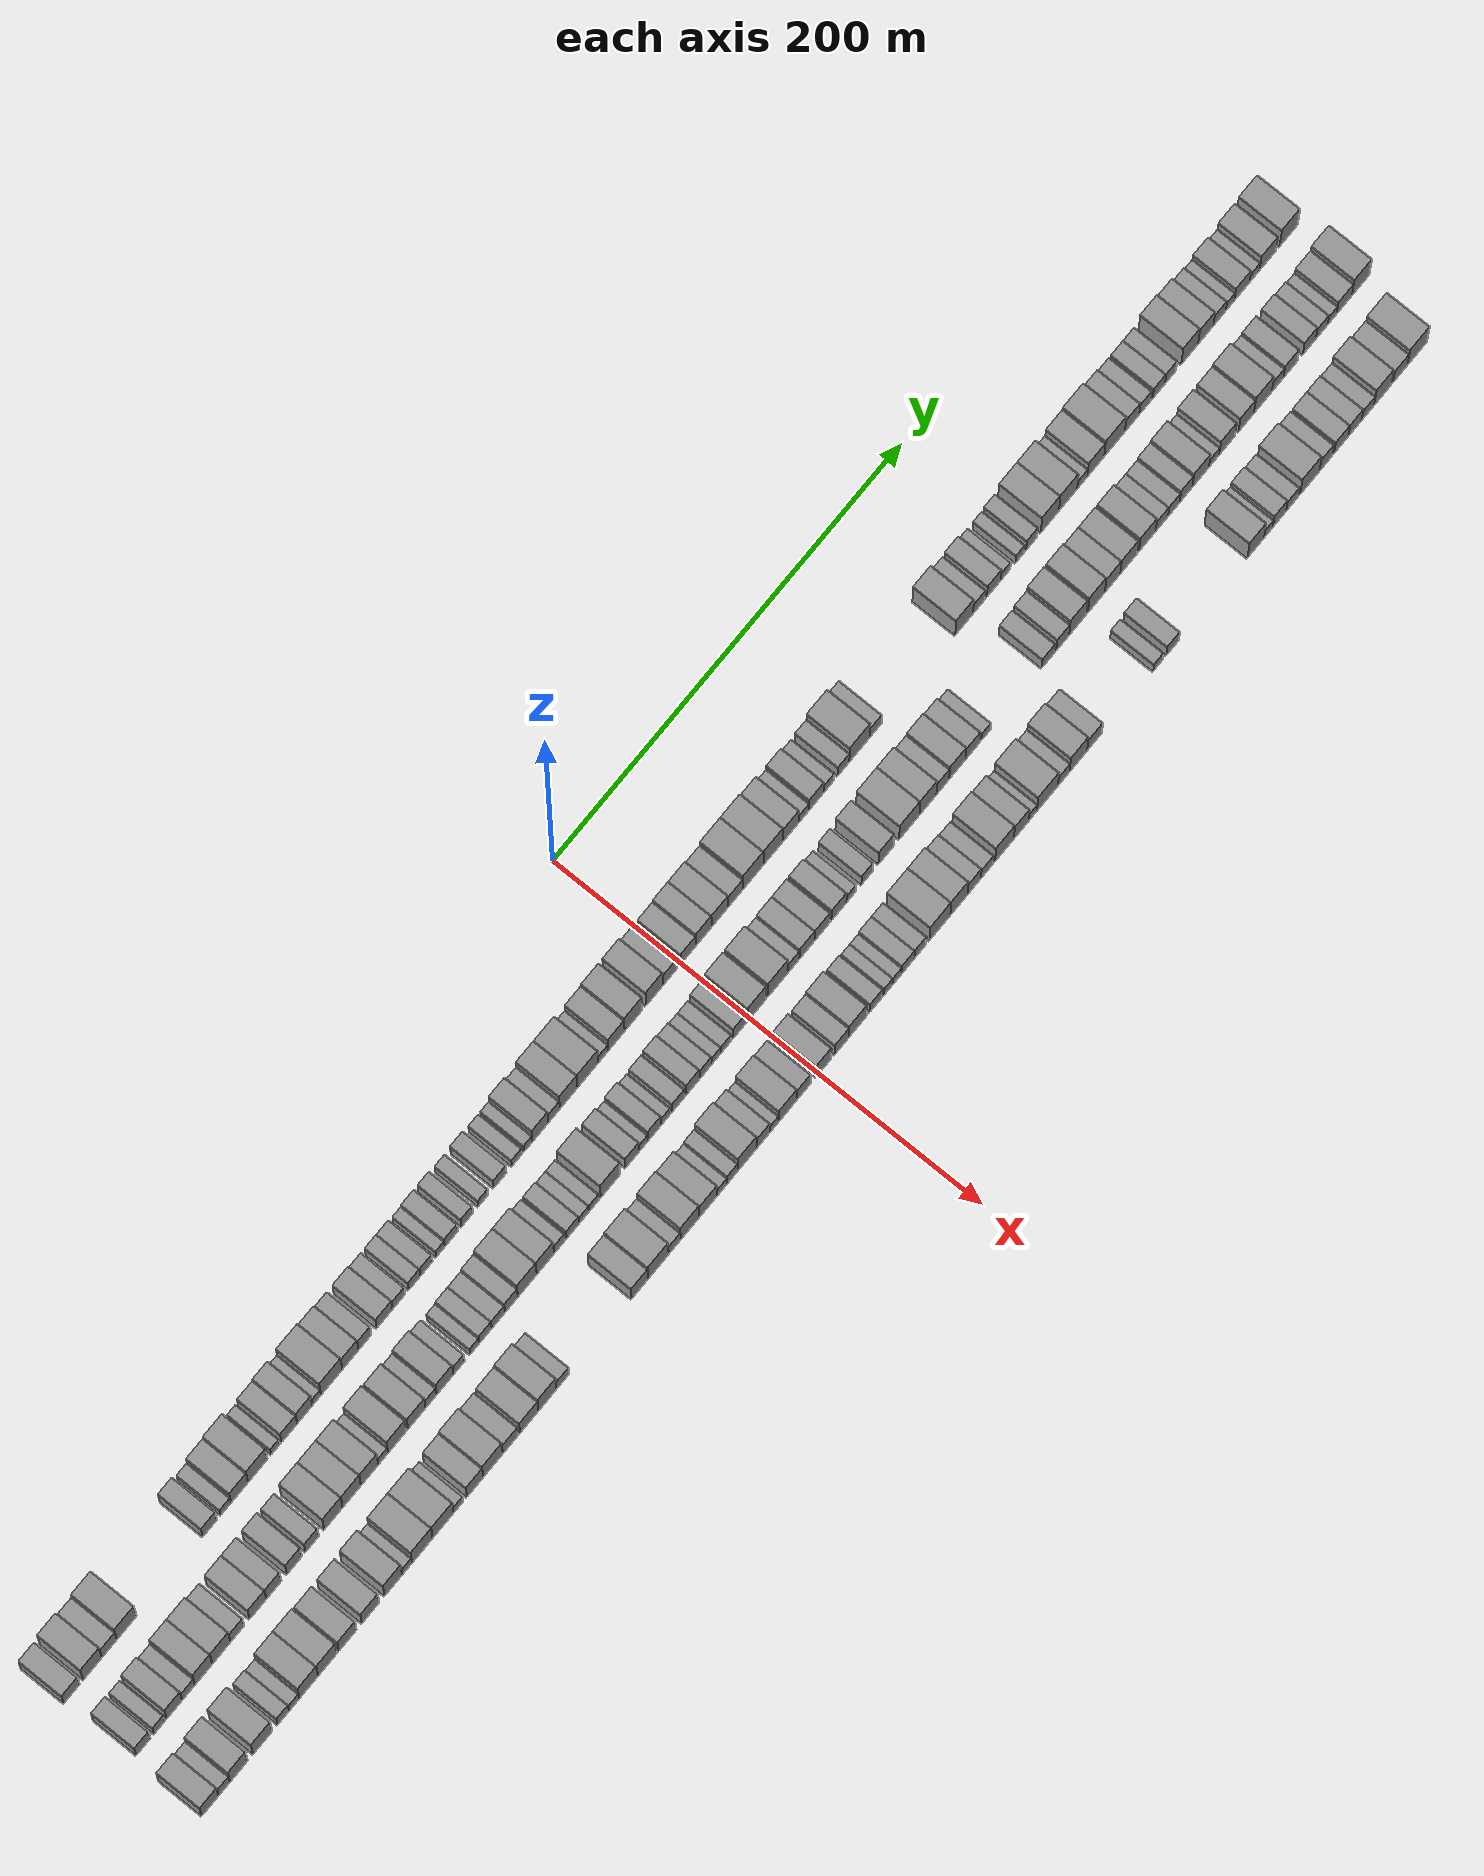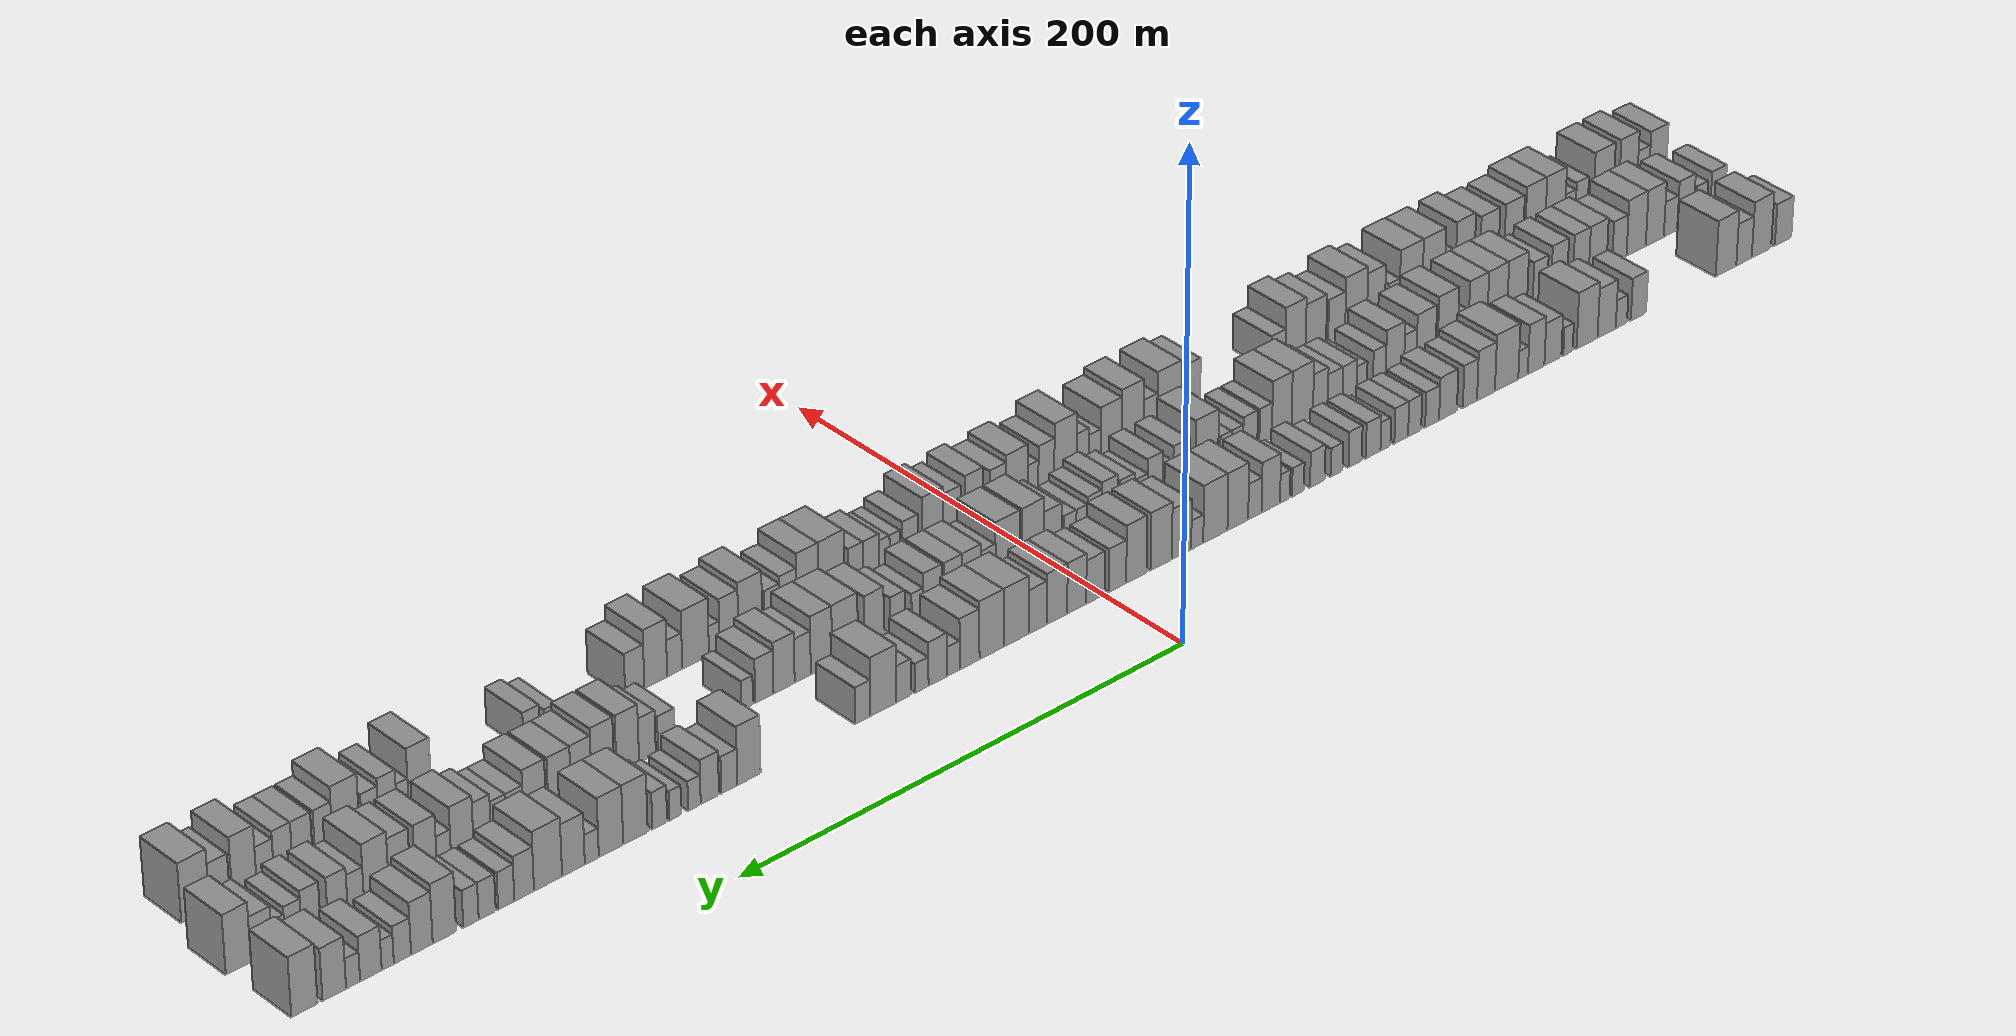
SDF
<sdf version="1.6">
 <world name="default">
  <scene>
   <sky><clouds><speed>12</speed></clouds></sky>
   <ambient>0.4 0.4 0.4 1</ambient>
   <background>0.7 0.7 0.7 1</background>
   <shadows>1</shadows>
  </scene>
  <gravity>0 0 -9.8066</gravity>
  <magnetic_field>6e-06 2.3e-05 -4.2e-05</magnetic_field>
  <physics default="0" name="default_physics" type="ode">
   <ode>
    <solver>
     <type>quick</type>
     <iters>10</iters>
     <sor>1.0</sor>
     <use_dynamic_moi_rescaling>0</use_dynamic_moi_rescaling>
    </solver>
    <constraints>
     <cfm>0</cfm>
     <erp>0.2</erp>
     <contact_max_correcting_vel>100</contact_max_correcting_vel>
     <contact_surface_layer>0.001</contact_surface_layer>
    </constraints>
   </ode>
   <max_step_size>0.004</max_step_size>
   <real_time_factor>1</real_time_factor>
   <real_time_update_rate>250</real_time_update_rate>
  </physics>
  <light name="sun" type="directional">
   <pose>0 0 10 0 0 0</pose>
   <diffuse>0.8 0.8 0.8 1</diffuse>
   <specular>0.2 0.2 0.2 1</specular>
   <attenuation>
    <range>1000</range>
    <constant>0.9</constant>
    <linear>0.01</linear>
    <quadratic>0.001</quadratic>
   </attenuation>
   <direction>-0.5 0.1 -0.9</direction>
  </light>
  <model name="building_1">
   <static>1</static>
   <pose>50.0000 -343.5456 0 0.000000 0.000000 0.000000</pose>
   <link name="link">
    <pose>0 0 9.00 0 0 0</pose>
    <collision name="collision"><geometry><box><size>20.0000 8.9087 18.0000</size></box></geometry></collision>
    <visual name="visual">
     <cast_shadows>0</cast_shadows>
     <geometry><box><size>20.0000 8.9087 18.0000</size></box></geometry>
     <material>
      <script>
       <uri>model://grey_wall/materials/scripts</uri>
       <uri>model://grey_wall/materials/textures</uri>
       <name>vrc/grey_wall</name>
      </script>
     </material>
    </visual>
   </link>
  </model>
  <model name="building_2">
   <static>1</static>
   <pose>50.0000 -331.8647 0 0.000000 0.000000 0.000000</pose>
   <link name="link">
    <pose>0 0 12.00 0 0 0</pose>
    <collision name="collision"><geometry><box><size>20.0000 10.4532 24.0000</size></box></geometry></collision>
    <visual name="visual">
     <cast_shadows>0</cast_shadows>
     <geometry><box><size>20.0000 10.4532 24.0000</size></box></geometry>
     <material>
      <script>
       <uri>model://grey_wall/materials/scripts</uri>
       <uri>model://grey_wall/materials/textures</uri>
       <name>vrc/grey_wall</name>
      </script>
     </material>
    </visual>
   </link>
  </model>
  <model name="building_3">
   <static>1</static>
   <pose>50.0000 -322.4770 0 0.000000 0.000000 0.000000</pose>
   <link name="link">
    <pose>0 0 9.00 0 0 0</pose>
    <collision name="collision"><geometry><box><size>20.0000 8.3221 18.0000</size></box></geometry></collision>
    <visual name="visual">
     <cast_shadows>0</cast_shadows>
     <geometry><box><size>20.0000 8.3221 18.0000</size></box></geometry>
     <material>
      <script>
       <uri>model://grey_wall/materials/scripts</uri>
       <uri>model://grey_wall/materials/textures</uri>
       <name>vrc/grey_wall</name>
      </script>
     </material>
    </visual>
   </link>
  </model>
  <model name="building_4">
   <static>1</static>
   <pose>50.0000 -312.7999 0 0.000000 0.000000 0.000000</pose>
   <link name="link">
    <pose>0 0 12.00 0 0 0</pose>
    <collision name="collision"><geometry><box><size>20.0000 11.0322 24.0000</size></box></geometry></collision>
    <visual name="visual">
     <cast_shadows>0</cast_shadows>
     <geometry><box><size>20.0000 11.0322 24.0000</size></box></geometry>
     <material>
      <script>
       <uri>model://grey_wall/materials/scripts</uri>
       <uri>model://grey_wall/materials/textures</uri>
       <name>vrc/grey_wall</name>
      </script>
     </material>
    </visual>
   </link>
  </model>
  <model name="building_5">
   <static>1</static>
   <pose>50.0000 -266.3293 0 0.000000 0.000000 0.000000</pose>
   <link name="link">
    <pose>0 0 9.00 0 0 0</pose>
    <collision name="collision"><geometry><box><size>20.0000 7.9696 18.0000</size></box></geometry></collision>
    <visual name="visual">
     <cast_shadows>0</cast_shadows>
     <geometry><box><size>20.0000 7.9696 18.0000</size></box></geometry>
     <material>
      <script>
       <uri>model://grey_wall/materials/scripts</uri>
       <uri>model://grey_wall/materials/textures</uri>
       <name>vrc/grey_wall</name>
      </script>
     </material>
    </visual>
   </link>
  </model>
  <model name="building_6">
   <static>1</static>
   <pose>50.0000 -257.3935 0 0.000000 0.000000 0.000000</pose>
   <link name="link">
    <pose>0 0 6.00 0 0 0</pose>
    <collision name="collision"><geometry><box><size>20.0000 5.9021 12.0000</size></box></geometry></collision>
    <visual name="visual">
     <cast_shadows>0</cast_shadows>
     <geometry><box><size>20.0000 5.9021 12.0000</size></box></geometry>
     <material>
      <script>
       <uri>model://grey_wall/materials/scripts</uri>
       <uri>model://grey_wall/materials/textures</uri>
       <name>vrc/grey_wall</name>
      </script>
     </material>
    </visual>
   </link>
  </model>
  <model name="building_7">
   <static>1</static>
   <pose>50.0000 -249.6908 0 0.000000 0.000000 0.000000</pose>
   <link name="link">
    <pose>0 0 10.50 0 0 0</pose>
    <collision name="collision"><geometry><box><size>20.0000 9.5032 21.0000</size></box></geometry></collision>
    <visual name="visual">
     <cast_shadows>0</cast_shadows>
     <geometry><box><size>20.0000 9.5032 21.0000</size></box></geometry>
     <material>
      <script>
       <uri>model://grey_wall/materials/scripts</uri>
       <uri>model://grey_wall/materials/textures</uri>
       <name>vrc/grey_wall</name>
      </script>
     </material>
    </visual>
   </link>
  </model>
  <model name="building_8">
   <static>1</static>
   <pose>50.0000 -239.4764 0 0.000000 0.000000 0.000000</pose>
   <link name="link">
    <pose>0 0 12.00 0 0 0</pose>
    <collision name="collision"><geometry><box><size>20.0000 10.9257 24.0000</size></box></geometry></collision>
    <visual name="visual">
     <cast_shadows>0</cast_shadows>
     <geometry><box><size>20.0000 10.9257 24.0000</size></box></geometry>
     <material>
      <script>
       <uri>model://grey_wall/materials/scripts</uri>
       <uri>model://grey_wall/materials/textures</uri>
       <name>vrc/grey_wall</name>
      </script>
     </material>
    </visual>
   </link>
  </model>
  <model name="building_9">
   <static>1</static>
   <pose>50.0000 -229.5694 0 0.000000 0.000000 0.000000</pose>
   <link name="link">
    <pose>0 0 6.00 0 0 0</pose>
    <collision name="collision"><geometry><box><size>20.0000 4.8882 12.0000</size></box></geometry></collision>
    <visual name="visual">
     <cast_shadows>0</cast_shadows>
     <geometry><box><size>20.0000 4.8882 12.0000</size></box></geometry>
     <material>
      <script>
       <uri>model://grey_wall/materials/scripts</uri>
       <uri>model://grey_wall/materials/textures</uri>
       <name>vrc/grey_wall</name>
      </script>
     </material>
    </visual>
   </link>
  </model>
  <model name="building_10">
   <static>1</static>
   <pose>50.0000 -221.7451 0 0.000000 0.000000 0.000000</pose>
   <link name="link">
    <pose>0 0 9.00 0 0 0</pose>
    <collision name="collision"><geometry><box><size>20.0000 8.7604 18.0000</size></box></geometry></collision>
    <visual name="visual">
     <cast_shadows>0</cast_shadows>
     <geometry><box><size>20.0000 8.7604 18.0000</size></box></geometry>
     <material>
      <script>
       <uri>model://grey_wall/materials/scripts</uri>
       <uri>model://grey_wall/materials/textures</uri>
       <name>vrc/grey_wall</name>
      </script>
     </material>
    </visual>
   </link>
  </model>
  <model name="building_11">
   <static>1</static>
   <pose>50.0000 -213.0992 0 0.000000 0.000000 0.000000</pose>
   <link name="link">
    <pose>0 0 10.50 0 0 0</pose>
    <collision name="collision"><geometry><box><size>20.0000 8.5314 21.0000</size></box></geometry></collision>
    <visual name="visual">
     <cast_shadows>0</cast_shadows>
     <geometry><box><size>20.0000 8.5314 21.0000</size></box></geometry>
     <material>
      <script>
       <uri>model://grey_wall/materials/scripts</uri>
       <uri>model://grey_wall/materials/textures</uri>
       <name>vrc/grey_wall</name>
      </script>
     </material>
    </visual>
   </link>
  </model>
  <model name="building_12">
   <static>1</static>
   <pose>50.0000 -206.3909 0 0.000000 0.000000 0.000000</pose>
   <link name="link">
    <pose>0 0 6.00 0 0 0</pose>
    <collision name="collision"><geometry><box><size>20.0000 4.8852 12.0000</size></box></geometry></collision>
    <visual name="visual">
     <cast_shadows>0</cast_shadows>
     <geometry><box><size>20.0000 4.8852 12.0000</size></box></geometry>
     <material>
      <script>
       <uri>model://grey_wall/materials/scripts</uri>
       <uri>model://grey_wall/materials/textures</uri>
       <name>vrc/grey_wall</name>
      </script>
     </material>
    </visual>
   </link>
  </model>
  <model name="building_13">
   <static>1</static>
   <pose>50.0000 -197.9598 0 0.000000 0.000000 0.000000</pose>
   <link name="link">
    <pose>0 0 12.00 0 0 0</pose>
    <collision name="collision"><geometry><box><size>20.0000 11.9770 24.0000</size></box></geometry></collision>
    <visual name="visual">
     <cast_shadows>0</cast_shadows>
     <geometry><box><size>20.0000 11.9770 24.0000</size></box></geometry>
     <material>
      <script>
       <uri>model://grey_wall/materials/scripts</uri>
       <uri>model://grey_wall/materials/textures</uri>
       <name>vrc/grey_wall</name>
      </script>
     </material>
    </visual>
   </link>
  </model>
  <model name="building_14">
   <static>1</static>
   <pose>50.0000 -187.4181 0 0.000000 0.000000 0.000000</pose>
   <link name="link">
    <pose>0 0 10.50 0 0 0</pose>
    <collision name="collision"><geometry><box><size>20.0000 9.1064 21.0000</size></box></geometry></collision>
    <visual name="visual">
     <cast_shadows>0</cast_shadows>
     <geometry><box><size>20.0000 9.1064 21.0000</size></box></geometry>
     <material>
      <script>
       <uri>model://grey_wall/materials/scripts</uri>
       <uri>model://grey_wall/materials/textures</uri>
       <name>vrc/grey_wall</name>
      </script>
     </material>
    </visual>
   </link>
  </model>
  <model name="building_15">
   <static>1</static>
   <pose>50.0000 -179.2638 0 0.000000 0.000000 0.000000</pose>
   <link name="link">
    <pose>0 0 9.00 0 0 0</pose>
    <collision name="collision"><geometry><box><size>20.0000 7.2021 18.0000</size></box></geometry></collision>
    <visual name="visual">
     <cast_shadows>0</cast_shadows>
     <geometry><box><size>20.0000 7.2021 18.0000</size></box></geometry>
     <material>
      <script>
       <uri>model://grey_wall/materials/scripts</uri>
       <uri>model://grey_wall/materials/textures</uri>
       <name>vrc/grey_wall</name>
      </script>
     </material>
    </visual>
   </link>
  </model>
  <model name="building_16">
   <static>1</static>
   <pose>50.0000 -168.1647 0 0.000000 0.000000 0.000000</pose>
   <link name="link">
    <pose>0 0 9.00 0 0 0</pose>
    <collision name="collision"><geometry><box><size>20.0000 8.9962 18.0000</size></box></geometry></collision>
    <visual name="visual">
     <cast_shadows>0</cast_shadows>
     <geometry><box><size>20.0000 8.9962 18.0000</size></box></geometry>
     <material>
      <script>
       <uri>model://grey_wall/materials/scripts</uri>
       <uri>model://grey_wall/materials/textures</uri>
       <name>vrc/grey_wall</name>
      </script>
     </material>
    </visual>
   </link>
  </model>
  <model name="building_17">
   <static>1</static>
   <pose>50.0000 -160.1435 0 0.000000 0.000000 0.000000</pose>
   <link name="link">
    <pose>0 0 7.50 0 0 0</pose>
    <collision name="collision"><geometry><box><size>20.0000 7.0462 15.0000</size></box></geometry></collision>
    <visual name="visual">
     <cast_shadows>0</cast_shadows>
     <geometry><box><size>20.0000 7.0462 15.0000</size></box></geometry>
     <material>
      <script>
       <uri>model://grey_wall/materials/scripts</uri>
       <uri>model://grey_wall/materials/textures</uri>
       <name>vrc/grey_wall</name>
      </script>
     </material>
    </visual>
   </link>
  </model>
  <model name="building_18">
   <static>1</static>
   <pose>50.0000 -151.3453 0 0.000000 0.000000 0.000000</pose>
   <link name="link">
    <pose>0 0 7.50 0 0 0</pose>
    <collision name="collision"><geometry><box><size>20.0000 6.5501 15.0000</size></box></geometry></collision>
    <visual name="visual">
     <cast_shadows>0</cast_shadows>
     <geometry><box><size>20.0000 6.5501 15.0000</size></box></geometry>
     <material>
      <script>
       <uri>model://grey_wall/materials/scripts</uri>
       <uri>model://grey_wall/materials/textures</uri>
       <name>vrc/grey_wall</name>
      </script>
     </material>
    </visual>
   </link>
  </model>
  <model name="building_19">
   <static>1</static>
   <pose>50.0000 -144.6323 0 0.000000 0.000000 0.000000</pose>
   <link name="link">
    <pose>0 0 7.50 0 0 0</pose>
    <collision name="collision"><geometry><box><size>20.0000 6.8760 15.0000</size></box></geometry></collision>
    <visual name="visual">
     <cast_shadows>0</cast_shadows>
     <geometry><box><size>20.0000 6.8760 15.0000</size></box></geometry>
     <material>
      <script>
       <uri>model://grey_wall/materials/scripts</uri>
       <uri>model://grey_wall/materials/textures</uri>
       <name>vrc/grey_wall</name>
      </script>
     </material>
    </visual>
   </link>
  </model>
  <model name="building_20">
   <static>1</static>
   <pose>50.0000 -136.7203 0 0.000000 0.000000 0.000000</pose>
   <link name="link">
    <pose>0 0 6.00 0 0 0</pose>
    <collision name="collision"><geometry><box><size>20.0000 4.9480 12.0000</size></box></geometry></collision>
    <visual name="visual">
     <cast_shadows>0</cast_shadows>
     <geometry><box><size>20.0000 4.9480 12.0000</size></box></geometry>
     <material>
      <script>
       <uri>model://grey_wall/materials/scripts</uri>
       <uri>model://grey_wall/materials/textures</uri>
       <name>vrc/grey_wall</name>
      </script>
     </material>
    </visual>
   </link>
  </model>
  <model name="building_21">
   <static>1</static>
   <pose>50.0000 -130.5726 0 0.000000 0.000000 0.000000</pose>
   <link name="link">
    <pose>0 0 7.50 0 0 0</pose>
    <collision name="collision"><geometry><box><size>20.0000 7.3475 15.0000</size></box></geometry></collision>
    <visual name="visual">
     <cast_shadows>0</cast_shadows>
     <geometry><box><size>20.0000 7.3475 15.0000</size></box></geometry>
     <material>
      <script>
       <uri>model://grey_wall/materials/scripts</uri>
       <uri>model://grey_wall/materials/textures</uri>
       <name>vrc/grey_wall</name>
      </script>
     </material>
    </visual>
   </link>
  </model>
  <model name="building_22">
   <static>1</static>
   <pose>50.0000 -121.6357 0 0.000000 0.000000 0.000000</pose>
   <link name="link">
    <pose>0 0 7.50 0 0 0</pose>
    <collision name="collision"><geometry><box><size>20.0000 6.5262 15.0000</size></box></geometry></collision>
    <visual name="visual">
     <cast_shadows>0</cast_shadows>
     <geometry><box><size>20.0000 6.5262 15.0000</size></box></geometry>
     <material>
      <script>
       <uri>model://grey_wall/materials/scripts</uri>
       <uri>model://grey_wall/materials/textures</uri>
       <name>vrc/grey_wall</name>
      </script>
     </material>
    </visual>
   </link>
  </model>
  <model name="building_23">
   <static>1</static>
   <pose>50.0000 -112.4987 0 0.000000 0.000000 0.000000</pose>
   <link name="link">
    <pose>0 0 6.00 0 0 0</pose>
    <collision name="collision"><geometry><box><size>20.0000 5.7479 12.0000</size></box></geometry></collision>
    <visual name="visual">
     <cast_shadows>0</cast_shadows>
     <geometry><box><size>20.0000 5.7479 12.0000</size></box></geometry>
     <material>
      <script>
       <uri>model://grey_wall/materials/scripts</uri>
       <uri>model://grey_wall/materials/textures</uri>
       <name>vrc/grey_wall</name>
      </script>
     </material>
    </visual>
   </link>
  </model>
  <model name="building_24">
   <static>1</static>
   <pose>50.0000 -102.9991 0 0.000000 0.000000 0.000000</pose>
   <link name="link">
    <pose>0 0 7.50 0 0 0</pose>
    <collision name="collision"><geometry><box><size>20.0000 7.2514 15.0000</size></box></geometry></collision>
    <visual name="visual">
     <cast_shadows>0</cast_shadows>
     <geometry><box><size>20.0000 7.2514 15.0000</size></box></geometry>
     <material>
      <script>
       <uri>model://grey_wall/materials/scripts</uri>
       <uri>model://grey_wall/materials/textures</uri>
       <name>vrc/grey_wall</name>
      </script>
     </material>
    </visual>
   </link>
  </model>
  <model name="building_25">
   <static>1</static>
   <pose>50.0000 -93.4552 0 0.000000 0.000000 0.000000</pose>
   <link name="link">
    <pose>0 0 6.00 0 0 0</pose>
    <collision name="collision"><geometry><box><size>20.0000 5.8363 12.0000</size></box></geometry></collision>
    <visual name="visual">
     <cast_shadows>0</cast_shadows>
     <geometry><box><size>20.0000 5.8363 12.0000</size></box></geometry>
     <material>
      <script>
       <uri>model://grey_wall/materials/scripts</uri>
       <uri>model://grey_wall/materials/textures</uri>
       <name>vrc/grey_wall</name>
      </script>
     </material>
    </visual>
   </link>
  </model>
  <model name="building_26">
   <static>1</static>
   <pose>50.0000 -87.1058 0 0.000000 0.000000 0.000000</pose>
   <link name="link">
    <pose>0 0 6.00 0 0 0</pose>
    <collision name="collision"><geometry><box><size>20.0000 4.8624 12.0000</size></box></geometry></collision>
    <visual name="visual">
     <cast_shadows>0</cast_shadows>
     <geometry><box><size>20.0000 4.8624 12.0000</size></box></geometry>
     <material>
      <script>
       <uri>model://grey_wall/materials/scripts</uri>
       <uri>model://grey_wall/materials/textures</uri>
       <name>vrc/grey_wall</name>
      </script>
     </material>
    </visual>
   </link>
  </model>
  <model name="building_27">
   <static>1</static>
   <pose>50.0000 -80.1643 0 0.000000 0.000000 0.000000</pose>
   <link name="link">
    <pose>0 0 10.50 0 0 0</pose>
    <collision name="collision"><geometry><box><size>20.0000 9.0205 21.0000</size></box></geometry></collision>
    <visual name="visual">
     <cast_shadows>0</cast_shadows>
     <geometry><box><size>20.0000 9.0205 21.0000</size></box></geometry>
     <material>
      <script>
       <uri>model://grey_wall/materials/scripts</uri>
       <uri>model://grey_wall/materials/textures</uri>
       <name>vrc/grey_wall</name>
      </script>
     </material>
    </visual>
   </link>
  </model>
  <model name="building_28">
   <static>1</static>
   <pose>50.0000 -72.4068 0 0.000000 0.000000 0.000000</pose>
   <link name="link">
    <pose>0 0 7.50 0 0 0</pose>
    <collision name="collision"><geometry><box><size>20.0000 6.4945 15.0000</size></box></geometry></collision>
    <visual name="visual">
     <cast_shadows>0</cast_shadows>
     <geometry><box><size>20.0000 6.4945 15.0000</size></box></geometry>
     <material>
      <script>
       <uri>model://grey_wall/materials/scripts</uri>
       <uri>model://grey_wall/materials/textures</uri>
       <name>vrc/grey_wall</name>
      </script>
     </material>
    </visual>
   </link>
  </model>
  <model name="building_29">
   <static>1</static>
   <pose>50.0000 -64.1397 0 0.000000 0.000000 0.000000</pose>
   <link name="link">
    <pose>0 0 12.00 0 0 0</pose>
    <collision name="collision"><geometry><box><size>20.0000 10.0398 24.0000</size></box></geometry></collision>
    <visual name="visual">
     <cast_shadows>0</cast_shadows>
     <geometry><box><size>20.0000 10.0398 24.0000</size></box></geometry>
     <material>
      <script>
       <uri>model://grey_wall/materials/scripts</uri>
       <uri>model://grey_wall/materials/textures</uri>
       <name>vrc/grey_wall</name>
      </script>
     </material>
    </visual>
   </link>
  </model>
  <model name="building_30">
   <static>1</static>
   <pose>50.0000 -53.2822 0 0.000000 0.000000 0.000000</pose>
   <link name="link">
    <pose>0 0 12.00 0 0 0</pose>
    <collision name="collision"><geometry><box><size>20.0000 11.6751 24.0000</size></box></geometry></collision>
    <visual name="visual">
     <cast_shadows>0</cast_shadows>
     <geometry><box><size>20.0000 11.6751 24.0000</size></box></geometry>
     <material>
      <script>
       <uri>model://grey_wall/materials/scripts</uri>
       <uri>model://grey_wall/materials/textures</uri>
       <name>vrc/grey_wall</name>
      </script>
     </material>
    </visual>
   </link>
  </model>
  <model name="building_31">
   <static>1</static>
   <pose>50.0000 -44.5478 0 0.000000 0.000000 0.000000</pose>
   <link name="link">
    <pose>0 0 6.00 0 0 0</pose>
    <collision name="collision"><geometry><box><size>20.0000 5.7937 12.0000</size></box></geometry></collision>
    <visual name="visual">
     <cast_shadows>0</cast_shadows>
     <geometry><box><size>20.0000 5.7937 12.0000</size></box></geometry>
     <material>
      <script>
       <uri>model://grey_wall/materials/scripts</uri>
       <uri>model://grey_wall/materials/textures</uri>
       <name>vrc/grey_wall</name>
      </script>
     </material>
    </visual>
   </link>
  </model>
  <model name="building_32">
   <static>1</static>
   <pose>50.0000 -37.0297 0 0.000000 0.000000 0.000000</pose>
   <link name="link">
    <pose>0 0 10.50 0 0 0</pose>
    <collision name="collision"><geometry><box><size>20.0000 9.2426 21.0000</size></box></geometry></collision>
    <visual name="visual">
     <cast_shadows>0</cast_shadows>
     <geometry><box><size>20.0000 9.2426 21.0000</size></box></geometry>
     <material>
      <script>
       <uri>model://grey_wall/materials/scripts</uri>
       <uri>model://grey_wall/materials/textures</uri>
       <name>vrc/grey_wall</name>
      </script>
     </material>
    </visual>
   </link>
  </model>
  <model name="building_33">
   <static>1</static>
   <pose>50.0000 -27.3568 0 0.000000 0.000000 0.000000</pose>
   <link name="link">
    <pose>0 0 12.00 0 0 0</pose>
    <collision name="collision"><geometry><box><size>20.0000 10.1032 24.0000</size></box></geometry></collision>
    <visual name="visual">
     <cast_shadows>0</cast_shadows>
     <geometry><box><size>20.0000 10.1032 24.0000</size></box></geometry>
     <material>
      <script>
       <uri>model://grey_wall/materials/scripts</uri>
       <uri>model://grey_wall/materials/textures</uri>
       <name>vrc/grey_wall</name>
      </script>
     </material>
    </visual>
   </link>
  </model>
  <model name="building_34">
   <static>1</static>
   <pose>50.0000 -15.4918 0 0.000000 0.000000 0.000000</pose>
   <link name="link">
    <pose>0 0 12.00 0 0 0</pose>
    <collision name="collision"><geometry><box><size>20.0000 9.6268 24.0000</size></box></geometry></collision>
    <visual name="visual">
     <cast_shadows>0</cast_shadows>
     <geometry><box><size>20.0000 9.6268 24.0000</size></box></geometry>
     <material>
      <script>
       <uri>model://grey_wall/materials/scripts</uri>
       <uri>model://grey_wall/materials/textures</uri>
       <name>vrc/grey_wall</name>
      </script>
     </material>
    </visual>
   </link>
  </model>
  <model name="building_35">
   <static>1</static>
   <pose>50.0000 -6.5953 0 0.000000 0.000000 0.000000</pose>
   <link name="link">
    <pose>0 0 9.00 0 0 0</pose>
    <collision name="collision"><geometry><box><size>20.0000 8.1662 18.0000</size></box></geometry></collision>
    <visual name="visual">
     <cast_shadows>0</cast_shadows>
     <geometry><box><size>20.0000 8.1662 18.0000</size></box></geometry>
     <material>
      <script>
       <uri>model://grey_wall/materials/scripts</uri>
       <uri>model://grey_wall/materials/textures</uri>
       <name>vrc/grey_wall</name>
      </script>
     </material>
    </visual>
   </link>
  </model>
  <model name="building_36">
   <static>1</static>
   <pose>50.0000 3.8273 0 0.000000 0.000000 0.000000</pose>
   <link name="link">
    <pose>0 0 9.00 0 0 0</pose>
    <collision name="collision"><geometry><box><size>20.0000 8.6790 18.0000</size></box></geometry></collision>
    <visual name="visual">
     <cast_shadows>0</cast_shadows>
     <geometry><box><size>20.0000 8.6790 18.0000</size></box></geometry>
     <material>
      <script>
       <uri>model://grey_wall/materials/scripts</uri>
       <uri>model://grey_wall/materials/textures</uri>
       <name>vrc/grey_wall</name>
      </script>
     </material>
    </visual>
   </link>
  </model>
  <model name="building_37">
   <static>1</static>
   <pose>50.0000 12.6170 0 0.000000 0.000000 0.000000</pose>
   <link name="link">
    <pose>0 0 10.50 0 0 0</pose>
    <collision name="collision"><geometry><box><size>20.0000 8.9003 21.0000</size></box></geometry></collision>
    <visual name="visual">
     <cast_shadows>0</cast_shadows>
     <geometry><box><size>20.0000 8.9003 21.0000</size></box></geometry>
     <material>
      <script>
       <uri>model://grey_wall/materials/scripts</uri>
       <uri>model://grey_wall/materials/textures</uri>
       <name>vrc/grey_wall</name>
      </script>
     </material>
    </visual>
   </link>
  </model>
  <model name="building_38">
   <static>1</static>
   <pose>50.0000 21.8389 0 0.000000 0.000000 0.000000</pose>
   <link name="link">
    <pose>0 0 10.50 0 0 0</pose>
    <collision name="collision"><geometry><box><size>20.0000 9.5435 21.0000</size></box></geometry></collision>
    <visual name="visual">
     <cast_shadows>0</cast_shadows>
     <geometry><box><size>20.0000 9.5435 21.0000</size></box></geometry>
     <material>
      <script>
       <uri>model://grey_wall/materials/scripts</uri>
       <uri>model://grey_wall/materials/textures</uri>
       <name>vrc/grey_wall</name>
      </script>
     </material>
    </visual>
   </link>
  </model>
  <model name="building_39">
   <static>1</static>
   <pose>50.0000 30.8368 0 0.000000 0.000000 0.000000</pose>
   <link name="link">
    <pose>0 0 9.00 0 0 0</pose>
    <collision name="collision"><geometry><box><size>20.0000 8.4524 18.0000</size></box></geometry></collision>
    <visual name="visual">
     <cast_shadows>0</cast_shadows>
     <geometry><box><size>20.0000 8.4524 18.0000</size></box></geometry>
     <material>
      <script>
       <uri>model://grey_wall/materials/scripts</uri>
       <uri>model://grey_wall/materials/textures</uri>
       <name>vrc/grey_wall</name>
      </script>
     </material>
    </visual>
   </link>
  </model>
  <model name="building_40">
   <static>1</static>
   <pose>50.0000 40.8845 0 0.000000 0.000000 0.000000</pose>
   <link name="link">
    <pose>0 0 12.00 0 0 0</pose>
    <collision name="collision"><geometry><box><size>20.0000 11.6430 24.0000</size></box></geometry></collision>
    <visual name="visual">
     <cast_shadows>0</cast_shadows>
     <geometry><box><size>20.0000 11.6430 24.0000</size></box></geometry>
     <material>
      <script>
       <uri>model://grey_wall/materials/scripts</uri>
       <uri>model://grey_wall/materials/textures</uri>
       <name>vrc/grey_wall</name>
      </script>
     </material>
    </visual>
   </link>
  </model>
  <model name="building_41">
   <static>1</static>
   <pose>50.0000 52.2881 0 0.000000 0.000000 0.000000</pose>
   <link name="link">
    <pose>0 0 12.00 0 0 0</pose>
    <collision name="collision"><geometry><box><size>20.0000 11.1642 24.0000</size></box></geometry></collision>
    <visual name="visual">
     <cast_shadows>0</cast_shadows>
     <geometry><box><size>20.0000 11.1642 24.0000</size></box></geometry>
     <material>
      <script>
       <uri>model://grey_wall/materials/scripts</uri>
       <uri>model://grey_wall/materials/textures</uri>
       <name>vrc/grey_wall</name>
      </script>
     </material>
    </visual>
   </link>
  </model>
  <model name="building_42">
   <static>1</static>
   <pose>50.0000 62.4153 0 0.000000 0.000000 0.000000</pose>
   <link name="link">
    <pose>0 0 10.50 0 0 0</pose>
    <collision name="collision"><geometry><box><size>20.0000 9.0902 21.0000</size></box></geometry></collision>
    <visual name="visual">
     <cast_shadows>0</cast_shadows>
     <geometry><box><size>20.0000 9.0902 21.0000</size></box></geometry>
     <material>
      <script>
       <uri>model://grey_wall/materials/scripts</uri>
       <uri>model://grey_wall/materials/textures</uri>
       <name>vrc/grey_wall</name>
      </script>
     </material>
    </visual>
   </link>
  </model>
  <model name="building_43">
   <static>1</static>
   <pose>50.0000 69.9059 0 0.000000 0.000000 0.000000</pose>
   <link name="link">
    <pose>0 0 6.00 0 0 0</pose>
    <collision name="collision"><geometry><box><size>20.0000 5.8910 12.0000</size></box></geometry></collision>
    <visual name="visual">
     <cast_shadows>0</cast_shadows>
     <geometry><box><size>20.0000 5.8910 12.0000</size></box></geometry>
     <material>
      <script>
       <uri>model://grey_wall/materials/scripts</uri>
       <uri>model://grey_wall/materials/textures</uri>
       <name>vrc/grey_wall</name>
      </script>
     </material>
    </visual>
   </link>
  </model>
  <model name="building_44">
   <static>1</static>
   <pose>50.0000 77.0381 0 0.000000 0.000000 0.000000</pose>
   <link name="link">
    <pose>0 0 9.00 0 0 0</pose>
    <collision name="collision"><geometry><box><size>20.0000 8.3734 18.0000</size></box></geometry></collision>
    <visual name="visual">
     <cast_shadows>0</cast_shadows>
     <geometry><box><size>20.0000 8.3734 18.0000</size></box></geometry>
     <material>
      <script>
       <uri>model://grey_wall/materials/scripts</uri>
       <uri>model://grey_wall/materials/textures</uri>
       <name>vrc/grey_wall</name>
      </script>
     </material>
    </visual>
   </link>
  </model>
  <model name="building_45">
   <static>1</static>
   <pose>50.0000 84.2231 0 0.000000 0.000000 0.000000</pose>
   <link name="link">
    <pose>0 0 6.00 0 0 0</pose>
    <collision name="collision"><geometry><box><size>20.0000 5.9965 12.0000</size></box></geometry></collision>
    <visual name="visual">
     <cast_shadows>0</cast_shadows>
     <geometry><box><size>20.0000 5.9965 12.0000</size></box></geometry>
     <material>
      <script>
       <uri>model://grey_wall/materials/scripts</uri>
       <uri>model://grey_wall/materials/textures</uri>
       <name>vrc/grey_wall</name>
      </script>
     </material>
    </visual>
   </link>
  </model>
  <model name="building_46">
   <static>1</static>
   <pose>50.0000 92.5135 0 0.000000 0.000000 0.000000</pose>
   <link name="link">
    <pose>0 0 7.50 0 0 0</pose>
    <collision name="collision"><geometry><box><size>20.0000 6.5844 15.0000</size></box></geometry></collision>
    <visual name="visual">
     <cast_shadows>0</cast_shadows>
     <geometry><box><size>20.0000 6.5844 15.0000</size></box></geometry>
     <material>
      <script>
       <uri>model://grey_wall/materials/scripts</uri>
       <uri>model://grey_wall/materials/textures</uri>
       <name>vrc/grey_wall</name>
      </script>
     </material>
    </visual>
   </link>
  </model>
  <model name="building_47">
   <static>1</static>
   <pose>50.0000 101.6979 0 0.000000 0.000000 0.000000</pose>
   <link name="link">
    <pose>0 0 12.00 0 0 0</pose>
    <collision name="collision"><geometry><box><size>20.0000 11.7844 24.0000</size></box></geometry></collision>
    <visual name="visual">
     <cast_shadows>0</cast_shadows>
     <geometry><box><size>20.0000 11.7844 24.0000</size></box></geometry>
     <material>
      <script>
       <uri>model://grey_wall/materials/scripts</uri>
       <uri>model://grey_wall/materials/textures</uri>
       <name>vrc/grey_wall</name>
      </script>
     </material>
    </visual>
   </link>
  </model>
  <model name="building_48">
   <static>1</static>
   <pose>50.0000 110.9772 0 0.000000 0.000000 0.000000</pose>
   <link name="link">
    <pose>0 0 7.50 0 0 0</pose>
    <collision name="collision"><geometry><box><size>20.0000 6.7743 15.0000</size></box></geometry></collision>
    <visual name="visual">
     <cast_shadows>0</cast_shadows>
     <geometry><box><size>20.0000 6.7743 15.0000</size></box></geometry>
     <material>
      <script>
       <uri>model://grey_wall/materials/scripts</uri>
       <uri>model://grey_wall/materials/textures</uri>
       <name>vrc/grey_wall</name>
      </script>
     </material>
    </visual>
   </link>
  </model>
  <model name="building_49">
   <static>1</static>
   <pose>50.0000 161.6814 0 0.000000 0.000000 0.000000</pose>
   <link name="link">
    <pose>0 0 12.00 0 0 0</pose>
    <collision name="collision"><geometry><box><size>20.0000 10.2114 24.0000</size></box></geometry></collision>
    <visual name="visual">
     <cast_shadows>0</cast_shadows>
     <geometry><box><size>20.0000 10.2114 24.0000</size></box></geometry>
     <material>
      <script>
       <uri>model://grey_wall/materials/scripts</uri>
       <uri>model://grey_wall/materials/textures</uri>
       <name>vrc/grey_wall</name>
      </script>
     </material>
    </visual>
   </link>
  </model>
  <model name="building_50">
   <static>1</static>
   <pose>50.0000 170.3060 0 0.000000 0.000000 0.000000</pose>
   <link name="link">
    <pose>0 0 7.50 0 0 0</pose>
    <collision name="collision"><geometry><box><size>20.0000 7.0377 15.0000</size></box></geometry></collision>
    <visual name="visual">
     <cast_shadows>0</cast_shadows>
     <geometry><box><size>20.0000 7.0377 15.0000</size></box></geometry>
     <material>
      <script>
       <uri>model://grey_wall/materials/scripts</uri>
       <uri>model://grey_wall/materials/textures</uri>
       <name>vrc/grey_wall</name>
      </script>
     </material>
    </visual>
   </link>
  </model>
  <model name="building_51">
   <static>1</static>
   <pose>50.0000 178.8272 0 0.000000 0.000000 0.000000</pose>
   <link name="link">
    <pose>0 0 9.00 0 0 0</pose>
    <collision name="collision"><geometry><box><size>20.0000 8.0048 18.0000</size></box></geometry></collision>
    <visual name="visual">
     <cast_shadows>0</cast_shadows>
     <geometry><box><size>20.0000 8.0048 18.0000</size></box></geometry>
     <material>
      <script>
       <uri>model://grey_wall/materials/scripts</uri>
       <uri>model://grey_wall/materials/textures</uri>
       <name>vrc/grey_wall</name>
      </script>
     </material>
    </visual>
   </link>
  </model>
  <model name="building_52">
   <static>1</static>
   <pose>50.0000 185.5706 0 0.000000 0.000000 0.000000</pose>
   <link name="link">
    <pose>0 0 6.00 0 0 0</pose>
    <collision name="collision"><geometry><box><size>20.0000 5.4821 12.0000</size></box></geometry></collision>
    <visual name="visual">
     <cast_shadows>0</cast_shadows>
     <geometry><box><size>20.0000 5.4821 12.0000</size></box></geometry>
     <material>
      <script>
       <uri>model://grey_wall/materials/scripts</uri>
       <uri>model://grey_wall/materials/textures</uri>
       <name>vrc/grey_wall</name>
      </script>
     </material>
    </visual>
   </link>
  </model>
  <model name="building_53">
   <static>1</static>
   <pose>50.0000 193.8831 0 0.000000 0.000000 0.000000</pose>
   <link name="link">
    <pose>0 0 6.00 0 0 0</pose>
    <collision name="collision"><geometry><box><size>20.0000 5.1428 12.0000</size></box></geometry></collision>
    <visual name="visual">
     <cast_shadows>0</cast_shadows>
     <geometry><box><size>20.0000 5.1428 12.0000</size></box></geometry>
     <material>
      <script>
       <uri>model://grey_wall/materials/scripts</uri>
       <uri>model://grey_wall/materials/textures</uri>
       <name>vrc/grey_wall</name>
      </script>
     </material>
    </visual>
   </link>
  </model>
  <model name="building_54">
   <static>1</static>
   <pose>50.0000 200.6551 0 0.000000 0.000000 0.000000</pose>
   <link name="link">
    <pose>0 0 7.50 0 0 0</pose>
    <collision name="collision"><geometry><box><size>20.0000 6.4012 15.0000</size></box></geometry></collision>
    <visual name="visual">
     <cast_shadows>0</cast_shadows>
     <geometry><box><size>20.0000 6.4012 15.0000</size></box></geometry>
     <material>
      <script>
       <uri>model://grey_wall/materials/scripts</uri>
       <uri>model://grey_wall/materials/textures</uri>
       <name>vrc/grey_wall</name>
      </script>
     </material>
    </visual>
   </link>
  </model>
  <model name="building_55">
   <static>1</static>
   <pose>50.0000 211.1271 0 0.000000 0.000000 0.000000</pose>
   <link name="link">
    <pose>0 0 12.00 0 0 0</pose>
    <collision name="collision"><geometry><box><size>20.0000 10.5428 24.0000</size></box></geometry></collision>
    <visual name="visual">
     <cast_shadows>0</cast_shadows>
     <geometry><box><size>20.0000 10.5428 24.0000</size></box></geometry>
     <material>
      <script>
       <uri>model://grey_wall/materials/scripts</uri>
       <uri>model://grey_wall/materials/textures</uri>
       <name>vrc/grey_wall</name>
      </script>
     </material>
    </visual>
   </link>
  </model>
  <model name="building_56">
   <static>1</static>
   <pose>50.0000 221.6350 0 0.000000 0.000000 0.000000</pose>
   <link name="link">
    <pose>0 0 12.00 0 0 0</pose>
    <collision name="collision"><geometry><box><size>20.0000 10.4730 24.0000</size></box></geometry></collision>
    <visual name="visual">
     <cast_shadows>0</cast_shadows>
     <geometry><box><size>20.0000 10.4730 24.0000</size></box></geometry>
     <material>
      <script>
       <uri>model://grey_wall/materials/scripts</uri>
       <uri>model://grey_wall/materials/textures</uri>
       <name>vrc/grey_wall</name>
      </script>
     </material>
    </visual>
   </link>
  </model>
  <model name="building_57">
   <static>1</static>
   <pose>50.0000 229.8627 0 0.000000 0.000000 0.000000</pose>
   <link name="link">
    <pose>0 0 6.00 0 0 0</pose>
    <collision name="collision"><geometry><box><size>20.0000 5.9825 12.0000</size></box></geometry></collision>
    <visual name="visual">
     <cast_shadows>0</cast_shadows>
     <geometry><box><size>20.0000 5.9825 12.0000</size></box></geometry>
     <material>
      <script>
       <uri>model://grey_wall/materials/scripts</uri>
       <uri>model://grey_wall/materials/textures</uri>
       <name>vrc/grey_wall</name>
      </script>
     </material>
    </visual>
   </link>
  </model>
  <model name="building_58">
   <static>1</static>
   <pose>50.0000 237.6955 0 0.000000 0.000000 0.000000</pose>
   <link name="link">
    <pose>0 0 10.50 0 0 0</pose>
    <collision name="collision"><geometry><box><size>20.0000 9.6830 21.0000</size></box></geometry></collision>
    <visual name="visual">
     <cast_shadows>0</cast_shadows>
     <geometry><box><size>20.0000 9.6830 21.0000</size></box></geometry>
     <material>
      <script>
       <uri>model://grey_wall/materials/scripts</uri>
       <uri>model://grey_wall/materials/textures</uri>
       <name>vrc/grey_wall</name>
      </script>
     </material>
    </visual>
   </link>
  </model>
  <model name="building_59">
   <static>1</static>
   <pose>50.0000 248.4919 0 0.000000 0.000000 0.000000</pose>
   <link name="link">
    <pose>0 0 12.00 0 0 0</pose>
    <collision name="collision"><geometry><box><size>20.0000 11.9099 24.0000</size></box></geometry></collision>
    <visual name="visual">
     <cast_shadows>0</cast_shadows>
     <geometry><box><size>20.0000 11.9099 24.0000</size></box></geometry>
     <material>
      <script>
       <uri>model://grey_wall/materials/scripts</uri>
       <uri>model://grey_wall/materials/textures</uri>
       <name>vrc/grey_wall</name>
      </script>
     </material>
    </visual>
   </link>
  </model>
  <model name="building_60">
   <static>1</static>
   <pose>50.0000 258.5899 0 0.000000 0.000000 0.000000</pose>
   <link name="link">
    <pose>0 0 9.00 0 0 0</pose>
    <collision name="collision"><geometry><box><size>20.0000 8.2860 18.0000</size></box></geometry></collision>
    <visual name="visual">
     <cast_shadows>0</cast_shadows>
     <geometry><box><size>20.0000 8.2860 18.0000</size></box></geometry>
     <material>
      <script>
       <uri>model://grey_wall/materials/scripts</uri>
       <uri>model://grey_wall/materials/textures</uri>
       <name>vrc/grey_wall</name>
      </script>
     </material>
    </visual>
   </link>
  </model>
  <model name="building_61">
   <static>1</static>
   <pose>50.0000 266.1512 0 0.000000 0.000000 0.000000</pose>
   <link name="link">
    <pose>0 0 7.50 0 0 0</pose>
    <collision name="collision"><geometry><box><size>20.0000 6.8367 15.0000</size></box></geometry></collision>
    <visual name="visual">
     <cast_shadows>0</cast_shadows>
     <geometry><box><size>20.0000 6.8367 15.0000</size></box></geometry>
     <material>
      <script>
       <uri>model://grey_wall/materials/scripts</uri>
       <uri>model://grey_wall/materials/textures</uri>
       <name>vrc/grey_wall</name>
      </script>
     </material>
    </visual>
   </link>
  </model>
  <model name="building_62">
   <static>1</static>
   <pose>50.0000 274.1442 0 0.000000 0.000000 0.000000</pose>
   <link name="link">
    <pose>0 0 7.50 0 0 0</pose>
    <collision name="collision"><geometry><box><size>20.0000 7.1492 15.0000</size></box></geometry></collision>
    <visual name="visual">
     <cast_shadows>0</cast_shadows>
     <geometry><box><size>20.0000 7.1492 15.0000</size></box></geometry>
     <material>
      <script>
       <uri>model://grey_wall/materials/scripts</uri>
       <uri>model://grey_wall/materials/textures</uri>
       <name>vrc/grey_wall</name>
      </script>
     </material>
    </visual>
   </link>
  </model>
  <model name="building_63">
   <static>1</static>
   <pose>50.0000 280.9306 0 0.000000 0.000000 0.000000</pose>
   <link name="link">
    <pose>0 0 7.50 0 0 0</pose>
    <collision name="collision"><geometry><box><size>20.0000 6.4235 15.0000</size></box></geometry></collision>
    <visual name="visual">
     <cast_shadows>0</cast_shadows>
     <geometry><box><size>20.0000 6.4235 15.0000</size></box></geometry>
     <material>
      <script>
       <uri>model://grey_wall/materials/scripts</uri>
       <uri>model://grey_wall/materials/textures</uri>
       <name>vrc/grey_wall</name>
      </script>
     </material>
    </visual>
   </link>
  </model>
  <model name="building_64">
   <static>1</static>
   <pose>50.0000 292.0159 0 0.000000 0.000000 0.000000</pose>
   <link name="link">
    <pose>0 0 12.00 0 0 0</pose>
    <collision name="collision"><geometry><box><size>20.0000 9.7471 24.0000</size></box></geometry></collision>
    <visual name="visual">
     <cast_shadows>0</cast_shadows>
     <geometry><box><size>20.0000 9.7471 24.0000</size></box></geometry>
     <material>
      <script>
       <uri>model://grey_wall/materials/scripts</uri>
       <uri>model://grey_wall/materials/textures</uri>
       <name>vrc/grey_wall</name>
      </script>
     </material>
    </visual>
   </link>
  </model>
  <model name="building_65">
   <static>1</static>
   <pose>50.0000 301.3566 0 0.000000 0.000000 0.000000</pose>
   <link name="link">
    <pose>0 0 10.50 0 0 0</pose>
    <collision name="collision"><geometry><box><size>20.0000 8.9344 21.0000</size></box></geometry></collision>
    <visual name="visual">
     <cast_shadows>0</cast_shadows>
     <geometry><box><size>20.0000 8.9344 21.0000</size></box></geometry>
     <material>
      <script>
       <uri>model://grey_wall/materials/scripts</uri>
       <uri>model://grey_wall/materials/textures</uri>
       <name>vrc/grey_wall</name>
      </script>
     </material>
    </visual>
   </link>
  </model>
  <model name="building_66">
   <static>1</static>
   <pose>50.0000 309.3874 0 0.000000 0.000000 0.000000</pose>
   <link name="link">
    <pose>0 0 7.50 0 0 0</pose>
    <collision name="collision"><geometry><box><size>20.0000 7.1272 15.0000</size></box></geometry></collision>
    <visual name="visual">
     <cast_shadows>0</cast_shadows>
     <geometry><box><size>20.0000 7.1272 15.0000</size></box></geometry>
     <material>
      <script>
       <uri>model://grey_wall/materials/scripts</uri>
       <uri>model://grey_wall/materials/textures</uri>
       <name>vrc/grey_wall</name>
      </script>
     </material>
    </visual>
   </link>
  </model>
  <model name="building_67">
   <static>1</static>
   <pose>50.0000 315.4517 0 0.000000 0.000000 0.000000</pose>
   <link name="link">
    <pose>0 0 6.00 0 0 0</pose>
    <collision name="collision"><geometry><box><size>20.0000 5.0014 12.0000</size></box></geometry></collision>
    <visual name="visual">
     <cast_shadows>0</cast_shadows>
     <geometry><box><size>20.0000 5.0014 12.0000</size></box></geometry>
     <material>
      <script>
       <uri>model://grey_wall/materials/scripts</uri>
       <uri>model://grey_wall/materials/textures</uri>
       <name>vrc/grey_wall</name>
      </script>
     </material>
    </visual>
   </link>
  </model>
  <model name="building_68">
   <static>1</static>
   <pose>50.0000 322.3887 0 0.000000 0.000000 0.000000</pose>
   <link name="link">
    <pose>0 0 9.00 0 0 0</pose>
    <collision name="collision"><geometry><box><size>20.0000 8.8725 18.0000</size></box></geometry></collision>
    <visual name="visual">
     <cast_shadows>0</cast_shadows>
     <geometry><box><size>20.0000 8.8725 18.0000</size></box></geometry>
     <material>
      <script>
       <uri>model://grey_wall/materials/scripts</uri>
       <uri>model://grey_wall/materials/textures</uri>
       <name>vrc/grey_wall</name>
      </script>
     </material>
    </visual>
   </link>
  </model>
  <model name="building_69">
   <static>1</static>
   <pose>50.0000 329.6839 0 0.000000 0.000000 0.000000</pose>
   <link name="link">
    <pose>0 0 6.00 0 0 0</pose>
    <collision name="collision"><geometry><box><size>20.0000 5.7180 12.0000</size></box></geometry></collision>
    <visual name="visual">
     <cast_shadows>0</cast_shadows>
     <geometry><box><size>20.0000 5.7180 12.0000</size></box></geometry>
     <material>
      <script>
       <uri>model://grey_wall/materials/scripts</uri>
       <uri>model://grey_wall/materials/textures</uri>
       <name>vrc/grey_wall</name>
      </script>
     </material>
    </visual>
   </link>
  </model>
  <model name="building_70">
   <static>1</static>
   <pose>50.0000 337.3587 0 0.000000 0.000000 0.000000</pose>
   <link name="link">
    <pose>0 0 10.50 0 0 0</pose>
    <collision name="collision"><geometry><box><size>20.0000 9.6316 21.0000</size></box></geometry></collision>
    <visual name="visual">
     <cast_shadows>0</cast_shadows>
     <geometry><box><size>20.0000 9.6316 21.0000</size></box></geometry>
     <material>
      <script>
       <uri>model://grey_wall/materials/scripts</uri>
       <uri>model://grey_wall/materials/textures</uri>
       <name>vrc/grey_wall</name>
      </script>
     </material>
    </visual>
   </link>
  </model>
  <model name="building_71">
   <static>1</static>
   <pose>50.0000 349.4940 0 0.000000 0.000000 0.000000</pose>
   <link name="link">
    <pose>0 0 12.00 0 0 0</pose>
    <collision name="collision"><geometry><box><size>20.0000 10.6389 24.0000</size></box></geometry></collision>
    <visual name="visual">
     <cast_shadows>0</cast_shadows>
     <geometry><box><size>20.0000 10.6389 24.0000</size></box></geometry>
     <material>
      <script>
       <uri>model://grey_wall/materials/scripts</uri>
       <uri>model://grey_wall/materials/textures</uri>
       <name>vrc/grey_wall</name>
      </script>
     </material>
    </visual>
   </link>
  </model>
  <model name="building_72">
   <static>1</static>
   <pose>82.0000 -342.0469 0 0.000000 0.000000 0.000000</pose>
   <link name="link">
    <pose>0 0 9.00 0 0 0</pose>
    <collision name="collision"><geometry><box><size>20.0000 7.9063 18.0000</size></box></geometry></collision>
    <visual name="visual">
     <cast_shadows>0</cast_shadows>
     <geometry><box><size>20.0000 7.9063 18.0000</size></box></geometry>
     <material>
      <script>
       <uri>model://grey_wall/materials/scripts</uri>
       <uri>model://grey_wall/materials/textures</uri>
       <name>vrc/grey_wall</name>
      </script>
     </material>
    </visual>
   </link>
  </model>
  <model name="building_73">
   <static>1</static>
   <pose>82.0000 -333.0649 0 0.000000 0.000000 0.000000</pose>
   <link name="link">
    <pose>0 0 7.50 0 0 0</pose>
    <collision name="collision"><geometry><box><size>20.0000 6.0577 15.0000</size></box></geometry></collision>
    <visual name="visual">
     <cast_shadows>0</cast_shadows>
     <geometry><box><size>20.0000 6.0577 15.0000</size></box></geometry>
     <material>
      <script>
       <uri>model://grey_wall/materials/scripts</uri>
       <uri>model://grey_wall/materials/textures</uri>
       <name>vrc/grey_wall</name>
      </script>
     </material>
    </visual>
   </link>
  </model>
  <model name="building_74">
   <static>1</static>
   <pose>82.0000 -324.7012 0 0.000000 0.000000 0.000000</pose>
   <link name="link">
    <pose>0 0 10.50 0 0 0</pose>
    <collision name="collision"><geometry><box><size>20.0000 8.6696 21.0000</size></box></geometry></collision>
    <visual name="visual">
     <cast_shadows>0</cast_shadows>
     <geometry><box><size>20.0000 8.6696 21.0000</size></box></geometry>
     <material>
      <script>
       <uri>model://grey_wall/materials/scripts</uri>
       <uri>model://grey_wall/materials/textures</uri>
       <name>vrc/grey_wall</name>
      </script>
     </material>
    </visual>
   </link>
  </model>
  <model name="building_75">
   <static>1</static>
   <pose>82.0000 -316.8048 0 0.000000 0.000000 0.000000</pose>
   <link name="link">
    <pose>0 0 7.50 0 0 0</pose>
    <collision name="collision"><geometry><box><size>20.0000 7.1232 15.0000</size></box></geometry></collision>
    <visual name="visual">
     <cast_shadows>0</cast_shadows>
     <geometry><box><size>20.0000 7.1232 15.0000</size></box></geometry>
     <material>
      <script>
       <uri>model://grey_wall/materials/scripts</uri>
       <uri>model://grey_wall/materials/textures</uri>
       <name>vrc/grey_wall</name>
      </script>
     </material>
    </visual>
   </link>
  </model>
  <model name="building_76">
   <static>1</static>
   <pose>82.0000 -308.4089 0 0.000000 0.000000 0.000000</pose>
   <link name="link">
    <pose>0 0 12.00 0 0 0</pose>
    <collision name="collision"><geometry><box><size>20.0000 9.6686 24.0000</size></box></geometry></collision>
    <visual name="visual">
     <cast_shadows>0</cast_shadows>
     <geometry><box><size>20.0000 9.6686 24.0000</size></box></geometry>
     <material>
      <script>
       <uri>model://grey_wall/materials/scripts</uri>
       <uri>model://grey_wall/materials/textures</uri>
       <name>vrc/grey_wall</name>
      </script>
     </material>
    </visual>
   </link>
  </model>
  <model name="building_77">
   <static>1</static>
   <pose>82.0000 -298.4523 0 0.000000 0.000000 0.000000</pose>
   <link name="link">
    <pose>0 0 12.00 0 0 0</pose>
    <collision name="collision"><geometry><box><size>20.0000 10.2447 24.0000</size></box></geometry></collision>
    <visual name="visual">
     <cast_shadows>0</cast_shadows>
     <geometry><box><size>20.0000 10.2447 24.0000</size></box></geometry>
     <material>
      <script>
       <uri>model://grey_wall/materials/scripts</uri>
       <uri>model://grey_wall/materials/textures</uri>
       <name>vrc/grey_wall</name>
      </script>
     </material>
    </visual>
   </link>
  </model>
  <model name="building_78">
   <static>1</static>
   <pose>82.0000 -289.5149 0 0.000000 0.000000 0.000000</pose>
   <link name="link">
    <pose>0 0 9.00 0 0 0</pose>
    <collision name="collision"><geometry><box><size>20.0000 7.6301 18.0000</size></box></geometry></collision>
    <visual name="visual">
     <cast_shadows>0</cast_shadows>
     <geometry><box><size>20.0000 7.6301 18.0000</size></box></geometry>
     <material>
      <script>
       <uri>model://grey_wall/materials/scripts</uri>
       <uri>model://grey_wall/materials/textures</uri>
       <name>vrc/grey_wall</name>
      </script>
     </material>
    </visual>
   </link>
  </model>
  <model name="building_79">
   <static>1</static>
   <pose>82.0000 -277.9944 0 0.000000 0.000000 0.000000</pose>
   <link name="link">
    <pose>0 0 10.50 0 0 0</pose>
    <collision name="collision"><geometry><box><size>20.0000 9.4110 21.0000</size></box></geometry></collision>
    <visual name="visual">
     <cast_shadows>0</cast_shadows>
     <geometry><box><size>20.0000 9.4110 21.0000</size></box></geometry>
     <material>
      <script>
       <uri>model://grey_wall/materials/scripts</uri>
       <uri>model://grey_wall/materials/textures</uri>
       <name>vrc/grey_wall</name>
      </script>
     </material>
    </visual>
   </link>
  </model>
  <model name="building_80">
   <static>1</static>
   <pose>82.0000 -269.0662 0 0.000000 0.000000 0.000000</pose>
   <link name="link">
    <pose>0 0 10.50 0 0 0</pose>
    <collision name="collision"><geometry><box><size>20.0000 8.4454 21.0000</size></box></geometry></collision>
    <visual name="visual">
     <cast_shadows>0</cast_shadows>
     <geometry><box><size>20.0000 8.4454 21.0000</size></box></geometry>
     <material>
      <script>
       <uri>model://grey_wall/materials/scripts</uri>
       <uri>model://grey_wall/materials/textures</uri>
       <name>vrc/grey_wall</name>
      </script>
     </material>
    </visual>
   </link>
  </model>
  <model name="building_81">
   <static>1</static>
   <pose>82.0000 -257.5932 0 0.000000 0.000000 0.000000</pose>
   <link name="link">
    <pose>0 0 10.50 0 0 0</pose>
    <collision name="collision"><geometry><box><size>20.0000 8.5006 21.0000</size></box></geometry></collision>
    <visual name="visual">
     <cast_shadows>0</cast_shadows>
     <geometry><box><size>20.0000 8.5006 21.0000</size></box></geometry>
     <material>
      <script>
       <uri>model://grey_wall/materials/scripts</uri>
       <uri>model://grey_wall/materials/textures</uri>
       <name>vrc/grey_wall</name>
      </script>
     </material>
    </visual>
   </link>
  </model>
  <model name="building_82">
   <static>1</static>
   <pose>82.0000 -247.6128 0 0.000000 0.000000 0.000000</pose>
   <link name="link">
    <pose>0 0 9.00 0 0 0</pose>
    <collision name="collision"><geometry><box><size>20.0000 7.4602 18.0000</size></box></geometry></collision>
    <visual name="visual">
     <cast_shadows>0</cast_shadows>
     <geometry><box><size>20.0000 7.4602 18.0000</size></box></geometry>
     <material>
      <script>
       <uri>model://grey_wall/materials/scripts</uri>
       <uri>model://grey_wall/materials/textures</uri>
       <name>vrc/grey_wall</name>
      </script>
     </material>
    </visual>
   </link>
  </model>
  <model name="building_83">
   <static>1</static>
   <pose>82.0000 -235.7181 0 0.000000 0.000000 0.000000</pose>
   <link name="link">
    <pose>0 0 12.00 0 0 0</pose>
    <collision name="collision"><geometry><box><size>20.0000 10.3291 24.0000</size></box></geometry></collision>
    <visual name="visual">
     <cast_shadows>0</cast_shadows>
     <geometry><box><size>20.0000 10.3291 24.0000</size></box></geometry>
     <material>
      <script>
       <uri>model://grey_wall/materials/scripts</uri>
       <uri>model://grey_wall/materials/textures</uri>
       <name>vrc/grey_wall</name>
      </script>
     </material>
    </visual>
   </link>
  </model>
  <model name="building_84">
   <static>1</static>
   <pose>82.0000 -225.4066 0 0.000000 0.000000 0.000000</pose>
   <link name="link">
    <pose>0 0 12.00 0 0 0</pose>
    <collision name="collision"><geometry><box><size>20.0000 10.2939 24.0000</size></box></geometry></collision>
    <visual name="visual">
     <cast_shadows>0</cast_shadows>
     <geometry><box><size>20.0000 10.2939 24.0000</size></box></geometry>
     <material>
      <script>
       <uri>model://grey_wall/materials/scripts</uri>
       <uri>model://grey_wall/materials/textures</uri>
       <name>vrc/grey_wall</name>
      </script>
     </material>
    </visual>
   </link>
  </model>
  <model name="building_85">
   <static>1</static>
   <pose>82.0000 -215.3774 0 0.000000 0.000000 0.000000</pose>
   <link name="link">
    <pose>0 0 12.00 0 0 0</pose>
    <collision name="collision"><geometry><box><size>20.0000 9.7645 24.0000</size></box></geometry></collision>
    <visual name="visual">
     <cast_shadows>0</cast_shadows>
     <geometry><box><size>20.0000 9.7645 24.0000</size></box></geometry>
     <material>
      <script>
       <uri>model://grey_wall/materials/scripts</uri>
       <uri>model://grey_wall/materials/textures</uri>
       <name>vrc/grey_wall</name>
      </script>
     </material>
    </visual>
   </link>
  </model>
  <model name="building_86">
   <static>1</static>
   <pose>82.0000 -207.7499 0 0.000000 0.000000 0.000000</pose>
   <link name="link">
    <pose>0 0 6.00 0 0 0</pose>
    <collision name="collision"><geometry><box><size>20.0000 5.4905 12.0000</size></box></geometry></collision>
    <visual name="visual">
     <cast_shadows>0</cast_shadows>
     <geometry><box><size>20.0000 5.4905 12.0000</size></box></geometry>
     <material>
      <script>
       <uri>model://grey_wall/materials/scripts</uri>
       <uri>model://grey_wall/materials/textures</uri>
       <name>vrc/grey_wall</name>
      </script>
     </material>
    </visual>
   </link>
  </model>
  <model name="building_87">
   <static>1</static>
   <pose>82.0000 -199.8691 0 0.000000 0.000000 0.000000</pose>
   <link name="link">
    <pose>0 0 12.00 0 0 0</pose>
    <collision name="collision"><geometry><box><size>20.0000 10.2711 24.0000</size></box></geometry></collision>
    <visual name="visual">
     <cast_shadows>0</cast_shadows>
     <geometry><box><size>20.0000 10.2711 24.0000</size></box></geometry>
     <material>
      <script>
       <uri>model://grey_wall/materials/scripts</uri>
       <uri>model://grey_wall/materials/textures</uri>
       <name>vrc/grey_wall</name>
      </script>
     </material>
    </visual>
   </link>
  </model>
  <model name="building_88">
   <static>1</static>
   <pose>82.0000 -188.8175 0 0.000000 0.000000 0.000000</pose>
   <link name="link">
    <pose>0 0 10.50 0 0 0</pose>
    <collision name="collision"><geometry><box><size>20.0000 9.8321 21.0000</size></box></geometry></collision>
    <visual name="visual">
     <cast_shadows>0</cast_shadows>
     <geometry><box><size>20.0000 9.8321 21.0000</size></box></geometry>
     <material>
      <script>
       <uri>model://grey_wall/materials/scripts</uri>
       <uri>model://grey_wall/materials/textures</uri>
       <name>vrc/grey_wall</name>
      </script>
     </material>
    </visual>
   </link>
  </model>
  <model name="building_89">
   <static>1</static>
   <pose>82.0000 -180.7747 0 0.000000 0.000000 0.000000</pose>
   <link name="link">
    <pose>0 0 7.50 0 0 0</pose>
    <collision name="collision"><geometry><box><size>20.0000 6.2535 15.0000</size></box></geometry></collision>
    <visual name="visual">
     <cast_shadows>0</cast_shadows>
     <geometry><box><size>20.0000 6.2535 15.0000</size></box></geometry>
     <material>
      <script>
       <uri>model://grey_wall/materials/scripts</uri>
       <uri>model://grey_wall/materials/textures</uri>
       <name>vrc/grey_wall</name>
      </script>
     </material>
    </visual>
   </link>
  </model>
  <model name="building_90">
   <static>1</static>
   <pose>82.0000 -172.9870 0 0.000000 0.000000 0.000000</pose>
   <link name="link">
    <pose>0 0 10.50 0 0 0</pose>
    <collision name="collision"><geometry><box><size>20.0000 9.3221 21.0000</size></box></geometry></collision>
    <visual name="visual">
     <cast_shadows>0</cast_shadows>
     <geometry><box><size>20.0000 9.3221 21.0000</size></box></geometry>
     <material>
      <script>
       <uri>model://grey_wall/materials/scripts</uri>
       <uri>model://grey_wall/materials/textures</uri>
       <name>vrc/grey_wall</name>
      </script>
     </material>
    </visual>
   </link>
  </model>
  <model name="building_91">
   <static>1</static>
   <pose>82.0000 -165.1076 0 0.000000 0.000000 0.000000</pose>
   <link name="link">
    <pose>0 0 7.50 0 0 0</pose>
    <collision name="collision"><geometry><box><size>20.0000 6.4365 15.0000</size></box></geometry></collision>
    <visual name="visual">
     <cast_shadows>0</cast_shadows>
     <geometry><box><size>20.0000 6.4365 15.0000</size></box></geometry>
     <material>
      <script>
       <uri>model://grey_wall/materials/scripts</uri>
       <uri>model://grey_wall/materials/textures</uri>
       <name>vrc/grey_wall</name>
      </script>
     </material>
    </visual>
   </link>
  </model>
  <model name="building_92">
   <static>1</static>
   <pose>82.0000 -156.3038 0 0.000000 0.000000 0.000000</pose>
   <link name="link">
    <pose>0 0 6.00 0 0 0</pose>
    <collision name="collision"><geometry><box><size>20.0000 5.1712 12.0000</size></box></geometry></collision>
    <visual name="visual">
     <cast_shadows>0</cast_shadows>
     <geometry><box><size>20.0000 5.1712 12.0000</size></box></geometry>
     <material>
      <script>
       <uri>model://grey_wall/materials/scripts</uri>
       <uri>model://grey_wall/materials/textures</uri>
       <name>vrc/grey_wall</name>
      </script>
     </material>
    </visual>
   </link>
  </model>
  <model name="building_93">
   <static>1</static>
   <pose>82.0000 -150.1644 0 0.000000 0.000000 0.000000</pose>
   <link name="link">
    <pose>0 0 7.50 0 0 0</pose>
    <collision name="collision"><geometry><box><size>20.0000 7.1075 15.0000</size></box></geometry></collision>
    <visual name="visual">
     <cast_shadows>0</cast_shadows>
     <geometry><box><size>20.0000 7.1075 15.0000</size></box></geometry>
     <material>
      <script>
       <uri>model://grey_wall/materials/scripts</uri>
       <uri>model://grey_wall/materials/textures</uri>
       <name>vrc/grey_wall</name>
      </script>
     </material>
    </visual>
   </link>
  </model>
  <model name="building_94">
   <static>1</static>
   <pose>82.0000 -142.8876 0 0.000000 0.000000 0.000000</pose>
   <link name="link">
    <pose>0 0 7.50 0 0 0</pose>
    <collision name="collision"><geometry><box><size>20.0000 7.4461 15.0000</size></box></geometry></collision>
    <visual name="visual">
     <cast_shadows>0</cast_shadows>
     <geometry><box><size>20.0000 7.4461 15.0000</size></box></geometry>
     <material>
      <script>
       <uri>model://grey_wall/materials/scripts</uri>
       <uri>model://grey_wall/materials/textures</uri>
       <name>vrc/grey_wall</name>
      </script>
     </material>
    </visual>
   </link>
  </model>
  <model name="building_95">
   <static>1</static>
   <pose>82.0000 -135.5089 0 0.000000 0.000000 0.000000</pose>
   <link name="link">
    <pose>0 0 9.00 0 0 0</pose>
    <collision name="collision"><geometry><box><size>20.0000 7.3113 18.0000</size></box></geometry></collision>
    <visual name="visual">
     <cast_shadows>0</cast_shadows>
     <geometry><box><size>20.0000 7.3113 18.0000</size></box></geometry>
     <material>
      <script>
       <uri>model://grey_wall/materials/scripts</uri>
       <uri>model://grey_wall/materials/textures</uri>
       <name>vrc/grey_wall</name>
      </script>
     </material>
    </visual>
   </link>
  </model>
  <model name="building_96">
   <static>1</static>
   <pose>82.0000 -126.5277 0 0.000000 0.000000 0.000000</pose>
   <link name="link">
    <pose>0 0 12.00 0 0 0</pose>
    <collision name="collision"><geometry><box><size>20.0000 10.6511 24.0000</size></box></geometry></collision>
    <visual name="visual">
     <cast_shadows>0</cast_shadows>
     <geometry><box><size>20.0000 10.6511 24.0000</size></box></geometry>
     <material>
      <script>
       <uri>model://grey_wall/materials/scripts</uri>
       <uri>model://grey_wall/materials/textures</uri>
       <name>vrc/grey_wall</name>
      </script>
     </material>
    </visual>
   </link>
  </model>
  <model name="building_97">
   <static>1</static>
   <pose>82.0000 -116.3429 0 0.000000 0.000000 0.000000</pose>
   <link name="link">
    <pose>0 0 12.00 0 0 0</pose>
    <collision name="collision"><geometry><box><size>20.0000 9.7185 24.0000</size></box></geometry></collision>
    <visual name="visual">
     <cast_shadows>0</cast_shadows>
     <geometry><box><size>20.0000 9.7185 24.0000</size></box></geometry>
     <material>
      <script>
       <uri>model://grey_wall/materials/scripts</uri>
       <uri>model://grey_wall/materials/textures</uri>
       <name>vrc/grey_wall</name>
      </script>
     </material>
    </visual>
   </link>
  </model>
  <model name="building_98">
   <static>1</static>
   <pose>82.0000 -108.3861 0 0.000000 0.000000 0.000000</pose>
   <link name="link">
    <pose>0 0 7.50 0 0 0</pose>
    <collision name="collision"><geometry><box><size>20.0000 6.1953 15.0000</size></box></geometry></collision>
    <visual name="visual">
     <cast_shadows>0</cast_shadows>
     <geometry><box><size>20.0000 6.1953 15.0000</size></box></geometry>
     <material>
      <script>
       <uri>model://grey_wall/materials/scripts</uri>
       <uri>model://grey_wall/materials/textures</uri>
       <name>vrc/grey_wall</name>
      </script>
     </material>
    </visual>
   </link>
  </model>
  <model name="building_99">
   <static>1</static>
   <pose>82.0000 -100.7794 0 0.000000 0.000000 0.000000</pose>
   <link name="link">
    <pose>0 0 7.50 0 0 0</pose>
    <collision name="collision"><geometry><box><size>20.0000 7.0181 15.0000</size></box></geometry></collision>
    <visual name="visual">
     <cast_shadows>0</cast_shadows>
     <geometry><box><size>20.0000 7.0181 15.0000</size></box></geometry>
     <material>
      <script>
       <uri>model://grey_wall/materials/scripts</uri>
       <uri>model://grey_wall/materials/textures</uri>
       <name>vrc/grey_wall</name>
      </script>
     </material>
    </visual>
   </link>
  </model>
  <model name="building_100">
   <static>1</static>
   <pose>82.0000 -94.3879 0 0.000000 0.000000 0.000000</pose>
   <link name="link">
    <pose>0 0 6.00 0 0 0</pose>
    <collision name="collision"><geometry><box><size>20.0000 5.7650 12.0000</size></box></geometry></collision>
    <visual name="visual">
     <cast_shadows>0</cast_shadows>
     <geometry><box><size>20.0000 5.7650 12.0000</size></box></geometry>
     <material>
      <script>
       <uri>model://grey_wall/materials/scripts</uri>
       <uri>model://grey_wall/materials/textures</uri>
       <name>vrc/grey_wall</name>
      </script>
     </material>
    </visual>
   </link>
  </model>
  <model name="building_101">
   <static>1</static>
   <pose>82.0000 -88.7665 0 0.000000 0.000000 0.000000</pose>
   <link name="link">
    <pose>0 0 6.00 0 0 0</pose>
    <collision name="collision"><geometry><box><size>20.0000 5.4777 12.0000</size></box></geometry></collision>
    <visual name="visual">
     <cast_shadows>0</cast_shadows>
     <geometry><box><size>20.0000 5.4777 12.0000</size></box></geometry>
     <material>
      <script>
       <uri>model://grey_wall/materials/scripts</uri>
       <uri>model://grey_wall/materials/textures</uri>
       <name>vrc/grey_wall</name>
      </script>
     </material>
    </visual>
   </link>
  </model>
  <model name="building_102">
   <static>1</static>
   <pose>82.0000 -79.4853 0 0.000000 0.000000 0.000000</pose>
   <link name="link">
    <pose>0 0 12.00 0 0 0</pose>
    <collision name="collision"><geometry><box><size>20.0000 11.0846 24.0000</size></box></geometry></collision>
    <visual name="visual">
     <cast_shadows>0</cast_shadows>
     <geometry><box><size>20.0000 11.0846 24.0000</size></box></geometry>
     <material>
      <script>
       <uri>model://grey_wall/materials/scripts</uri>
       <uri>model://grey_wall/materials/textures</uri>
       <name>vrc/grey_wall</name>
      </script>
     </material>
    </visual>
   </link>
  </model>
  <model name="building_103">
   <static>1</static>
   <pose>82.0000 -67.0292 0 0.000000 0.000000 0.000000</pose>
   <link name="link">
    <pose>0 0 9.00 0 0 0</pose>
    <collision name="collision"><geometry><box><size>20.0000 7.8277 18.0000</size></box></geometry></collision>
    <visual name="visual">
     <cast_shadows>0</cast_shadows>
     <geometry><box><size>20.0000 7.8277 18.0000</size></box></geometry>
     <material>
      <script>
       <uri>model://grey_wall/materials/scripts</uri>
       <uri>model://grey_wall/materials/textures</uri>
       <name>vrc/grey_wall</name>
      </script>
     </material>
    </visual>
   </link>
  </model>
  <model name="building_104">
   <static>1</static>
   <pose>82.0000 -60.6409 0 0.000000 0.000000 0.000000</pose>
   <link name="link">
    <pose>0 0 6.00 0 0 0</pose>
    <collision name="collision"><geometry><box><size>20.0000 4.9489 12.0000</size></box></geometry></collision>
    <visual name="visual">
     <cast_shadows>0</cast_shadows>
     <geometry><box><size>20.0000 4.9489 12.0000</size></box></geometry>
     <material>
      <script>
       <uri>model://grey_wall/materials/scripts</uri>
       <uri>model://grey_wall/materials/textures</uri>
       <name>vrc/grey_wall</name>
      </script>
     </material>
    </visual>
   </link>
  </model>
  <model name="building_105">
   <static>1</static>
   <pose>82.0000 -54.4743 0 0.000000 0.000000 0.000000</pose>
   <link name="link">
    <pose>0 0 9.00 0 0 0</pose>
    <collision name="collision"><geometry><box><size>20.0000 7.3844 18.0000</size></box></geometry></collision>
    <visual name="visual">
     <cast_shadows>0</cast_shadows>
     <geometry><box><size>20.0000 7.3844 18.0000</size></box></geometry>
     <material>
      <script>
       <uri>model://grey_wall/materials/scripts</uri>
       <uri>model://grey_wall/materials/textures</uri>
       <name>vrc/grey_wall</name>
      </script>
     </material>
    </visual>
   </link>
  </model>
  <model name="building_106">
   <static>1</static>
   <pose>82.0000 -48.0901 0 0.000000 0.000000 0.000000</pose>
   <link name="link">
    <pose>0 0 6.00 0 0 0</pose>
    <collision name="collision"><geometry><box><size>20.0000 5.3839 12.0000</size></box></geometry></collision>
    <visual name="visual">
     <cast_shadows>0</cast_shadows>
     <geometry><box><size>20.0000 5.3839 12.0000</size></box></geometry>
     <material>
      <script>
       <uri>model://grey_wall/materials/scripts</uri>
       <uri>model://grey_wall/materials/textures</uri>
       <name>vrc/grey_wall</name>
      </script>
     </material>
    </visual>
   </link>
  </model>
  <model name="building_107">
   <static>1</static>
   <pose>82.0000 -40.8551 0 0.000000 0.000000 0.000000</pose>
   <link name="link">
    <pose>0 0 7.50 0 0 0</pose>
    <collision name="collision"><geometry><box><size>20.0000 7.0862 15.0000</size></box></geometry></collision>
    <visual name="visual">
     <cast_shadows>0</cast_shadows>
     <geometry><box><size>20.0000 7.0862 15.0000</size></box></geometry>
     <material>
      <script>
       <uri>model://grey_wall/materials/scripts</uri>
       <uri>model://grey_wall/materials/textures</uri>
       <name>vrc/grey_wall</name>
      </script>
     </material>
    </visual>
   </link>
  </model>
  <model name="building_108">
   <static>1</static>
   <pose>82.0000 -32.5612 0 0.000000 0.000000 0.000000</pose>
   <link name="link">
    <pose>0 0 9.00 0 0 0</pose>
    <collision name="collision"><geometry><box><size>20.0000 7.5016 18.0000</size></box></geometry></collision>
    <visual name="visual">
     <cast_shadows>0</cast_shadows>
     <geometry><box><size>20.0000 7.5016 18.0000</size></box></geometry>
     <material>
      <script>
       <uri>model://grey_wall/materials/scripts</uri>
       <uri>model://grey_wall/materials/textures</uri>
       <name>vrc/grey_wall</name>
      </script>
     </material>
    </visual>
   </link>
  </model>
  <model name="building_109">
   <static>1</static>
   <pose>82.0000 -25.4189 0 0.000000 0.000000 0.000000</pose>
   <link name="link">
    <pose>0 0 7.50 0 0 0</pose>
    <collision name="collision"><geometry><box><size>20.0000 6.7830 15.0000</size></box></geometry></collision>
    <visual name="visual">
     <cast_shadows>0</cast_shadows>
     <geometry><box><size>20.0000 6.7830 15.0000</size></box></geometry>
     <material>
      <script>
       <uri>model://grey_wall/materials/scripts</uri>
       <uri>model://grey_wall/materials/textures</uri>
       <name>vrc/grey_wall</name>
      </script>
     </material>
    </visual>
   </link>
  </model>
  <model name="building_110">
   <static>1</static>
   <pose>82.0000 -19.3626 0 0.000000 0.000000 0.000000</pose>
   <link name="link">
    <pose>0 0 6.00 0 0 0</pose>
    <collision name="collision"><geometry><box><size>20.0000 5.3297 12.0000</size></box></geometry></collision>
    <visual name="visual">
     <cast_shadows>0</cast_shadows>
     <geometry><box><size>20.0000 5.3297 12.0000</size></box></geometry>
     <material>
      <script>
       <uri>model://grey_wall/materials/scripts</uri>
       <uri>model://grey_wall/materials/textures</uri>
       <name>vrc/grey_wall</name>
      </script>
     </material>
    </visual>
   </link>
  </model>
  <model name="building_111">
   <static>1</static>
   <pose>82.0000 -13.7216 0 0.000000 0.000000 0.000000</pose>
   <link name="link">
    <pose>0 0 6.00 0 0 0</pose>
    <collision name="collision"><geometry><box><size>20.0000 5.9522 12.0000</size></box></geometry></collision>
    <visual name="visual">
     <cast_shadows>0</cast_shadows>
     <geometry><box><size>20.0000 5.9522 12.0000</size></box></geometry>
     <material>
      <script>
       <uri>model://grey_wall/materials/scripts</uri>
       <uri>model://grey_wall/materials/textures</uri>
       <name>vrc/grey_wall</name>
      </script>
     </material>
    </visual>
   </link>
  </model>
  <model name="building_112">
   <static>1</static>
   <pose>82.0000 -5.6288 0 0.000000 0.000000 0.000000</pose>
   <link name="link">
    <pose>0 0 9.00 0 0 0</pose>
    <collision name="collision"><geometry><box><size>20.0000 8.2335 18.0000</size></box></geometry></collision>
    <visual name="visual">
     <cast_shadows>0</cast_shadows>
     <geometry><box><size>20.0000 8.2335 18.0000</size></box></geometry>
     <material>
      <script>
       <uri>model://grey_wall/materials/scripts</uri>
       <uri>model://grey_wall/materials/textures</uri>
       <name>vrc/grey_wall</name>
      </script>
     </material>
    </visual>
   </link>
  </model>
  <model name="building_113">
   <static>1</static>
   <pose>82.0000 3.7728 0 0.000000 0.000000 0.000000</pose>
   <link name="link">
    <pose>0 0 12.00 0 0 0</pose>
    <collision name="collision"><geometry><box><size>20.0000 10.5697 24.0000</size></box></geometry></collision>
    <visual name="visual">
     <cast_shadows>0</cast_shadows>
     <geometry><box><size>20.0000 10.5697 24.0000</size></box></geometry>
     <material>
      <script>
       <uri>model://grey_wall/materials/scripts</uri>
       <uri>model://grey_wall/materials/textures</uri>
       <name>vrc/grey_wall</name>
      </script>
     </material>
    </visual>
   </link>
  </model>
  <model name="building_114">
   <static>1</static>
   <pose>82.0000 15.7465 0 0.000000 0.000000 0.000000</pose>
   <link name="link">
    <pose>0 0 12.00 0 0 0</pose>
    <collision name="collision"><geometry><box><size>20.0000 11.3777 24.0000</size></box></geometry></collision>
    <visual name="visual">
     <cast_shadows>0</cast_shadows>
     <geometry><box><size>20.0000 11.3777 24.0000</size></box></geometry>
     <material>
      <script>
       <uri>model://grey_wall/materials/scripts</uri>
       <uri>model://grey_wall/materials/textures</uri>
       <name>vrc/grey_wall</name>
      </script>
     </material>
    </visual>
   </link>
  </model>
  <model name="building_115">
   <static>1</static>
   <pose>82.0000 24.7164 0 0.000000 0.000000 0.000000</pose>
   <link name="link">
    <pose>0 0 7.50 0 0 0</pose>
    <collision name="collision"><geometry><box><size>20.0000 6.5621 15.0000</size></box></geometry></collision>
    <visual name="visual">
     <cast_shadows>0</cast_shadows>
     <geometry><box><size>20.0000 6.5621 15.0000</size></box></geometry>
     <material>
      <script>
       <uri>model://grey_wall/materials/scripts</uri>
       <uri>model://grey_wall/materials/textures</uri>
       <name>vrc/grey_wall</name>
      </script>
     </material>
    </visual>
   </link>
  </model>
  <model name="building_116">
   <static>1</static>
   <pose>82.0000 32.4088 0 0.000000 0.000000 0.000000</pose>
   <link name="link">
    <pose>0 0 9.00 0 0 0</pose>
    <collision name="collision"><geometry><box><size>20.0000 8.8228 18.0000</size></box></geometry></collision>
    <visual name="visual">
     <cast_shadows>0</cast_shadows>
     <geometry><box><size>20.0000 8.8228 18.0000</size></box></geometry>
     <material>
      <script>
       <uri>model://grey_wall/materials/scripts</uri>
       <uri>model://grey_wall/materials/textures</uri>
       <name>vrc/grey_wall</name>
      </script>
     </material>
    </visual>
   </link>
  </model>
  <model name="building_117">
   <static>1</static>
   <pose>82.0000 41.1415 0 0.000000 0.000000 0.000000</pose>
   <link name="link">
    <pose>0 0 9.00 0 0 0</pose>
    <collision name="collision"><geometry><box><size>20.0000 8.6426 18.0000</size></box></geometry></collision>
    <visual name="visual">
     <cast_shadows>0</cast_shadows>
     <geometry><box><size>20.0000 8.6426 18.0000</size></box></geometry>
     <material>
      <script>
       <uri>model://grey_wall/materials/scripts</uri>
       <uri>model://grey_wall/materials/textures</uri>
       <name>vrc/grey_wall</name>
      </script>
     </material>
    </visual>
   </link>
  </model>
  <model name="building_118">
   <static>1</static>
   <pose>82.0000 50.6567 0 0.000000 0.000000 0.000000</pose>
   <link name="link">
    <pose>0 0 9.00 0 0 0</pose>
    <collision name="collision"><geometry><box><size>20.0000 8.3878 18.0000</size></box></geometry></collision>
    <visual name="visual">
     <cast_shadows>0</cast_shadows>
     <geometry><box><size>20.0000 8.3878 18.0000</size></box></geometry>
     <material>
      <script>
       <uri>model://grey_wall/materials/scripts</uri>
       <uri>model://grey_wall/materials/textures</uri>
       <name>vrc/grey_wall</name>
      </script>
     </material>
    </visual>
   </link>
  </model>
  <model name="building_119">
   <static>1</static>
   <pose>82.0000 57.6190 0 0.000000 0.000000 0.000000</pose>
   <link name="link">
    <pose>0 0 6.00 0 0 0</pose>
    <collision name="collision"><geometry><box><size>20.0000 5.5368 12.0000</size></box></geometry></collision>
    <visual name="visual">
     <cast_shadows>0</cast_shadows>
     <geometry><box><size>20.0000 5.5368 12.0000</size></box></geometry>
     <material>
      <script>
       <uri>model://grey_wall/materials/scripts</uri>
       <uri>model://grey_wall/materials/textures</uri>
       <name>vrc/grey_wall</name>
      </script>
     </material>
    </visual>
   </link>
  </model>
  <model name="building_120">
   <static>1</static>
   <pose>82.0000 66.7506 0 0.000000 0.000000 0.000000</pose>
   <link name="link">
    <pose>0 0 7.50 0 0 0</pose>
    <collision name="collision"><geometry><box><size>20.0000 6.7265 15.0000</size></box></geometry></collision>
    <visual name="visual">
     <cast_shadows>0</cast_shadows>
     <geometry><box><size>20.0000 6.7265 15.0000</size></box></geometry>
     <material>
      <script>
       <uri>model://grey_wall/materials/scripts</uri>
       <uri>model://grey_wall/materials/textures</uri>
       <name>vrc/grey_wall</name>
      </script>
     </material>
    </visual>
   </link>
  </model>
  <model name="building_121">
   <static>1</static>
   <pose>82.0000 77.5383 0 0.000000 0.000000 0.000000</pose>
   <link name="link">
    <pose>0 0 10.50 0 0 0</pose>
    <collision name="collision"><geometry><box><size>20.0000 8.8488 21.0000</size></box></geometry></collision>
    <visual name="visual">
     <cast_shadows>0</cast_shadows>
     <geometry><box><size>20.0000 8.8488 21.0000</size></box></geometry>
     <material>
      <script>
       <uri>model://grey_wall/materials/scripts</uri>
       <uri>model://grey_wall/materials/textures</uri>
       <name>vrc/grey_wall</name>
      </script>
     </material>
    </visual>
   </link>
  </model>
  <model name="building_122">
   <static>1</static>
   <pose>82.0000 90.8329 0 0.000000 0.000000 0.000000</pose>
   <link name="link">
    <pose>0 0 12.00 0 0 0</pose>
    <collision name="collision"><geometry><box><size>20.0000 11.7405 24.0000</size></box></geometry></collision>
    <visual name="visual">
     <cast_shadows>0</cast_shadows>
     <geometry><box><size>20.0000 11.7405 24.0000</size></box></geometry>
     <material>
      <script>
       <uri>model://grey_wall/materials/scripts</uri>
       <uri>model://grey_wall/materials/textures</uri>
       <name>vrc/grey_wall</name>
      </script>
     </material>
    </visual>
   </link>
  </model>
  <model name="building_123">
   <static>1</static>
   <pose>82.0000 101.5374 0 0.000000 0.000000 0.000000</pose>
   <link name="link">
    <pose>0 0 12.00 0 0 0</pose>
    <collision name="collision"><geometry><box><size>20.0000 9.6685 24.0000</size></box></geometry></collision>
    <visual name="visual">
     <cast_shadows>0</cast_shadows>
     <geometry><box><size>20.0000 9.6685 24.0000</size></box></geometry>
     <material>
      <script>
       <uri>model://grey_wall/materials/scripts</uri>
       <uri>model://grey_wall/materials/textures</uri>
       <name>vrc/grey_wall</name>
      </script>
     </material>
    </visual>
   </link>
  </model>
  <model name="building_124">
   <static>1</static>
   <pose>82.0000 110.0228 0 0.000000 0.000000 0.000000</pose>
   <link name="link">
    <pose>0 0 9.00 0 0 0</pose>
    <collision name="collision"><geometry><box><size>20.0000 7.3022 18.0000</size></box></geometry></collision>
    <visual name="visual">
     <cast_shadows>0</cast_shadows>
     <geometry><box><size>20.0000 7.3022 18.0000</size></box></geometry>
     <material>
      <script>
       <uri>model://grey_wall/materials/scripts</uri>
       <uri>model://grey_wall/materials/textures</uri>
       <name>vrc/grey_wall</name>
      </script>
     </material>
    </visual>
   </link>
  </model>
  <model name="building_125">
   <static>1</static>
   <pose>82.0000 118.4263 0 0.000000 0.000000 0.000000</pose>
   <link name="link">
    <pose>0 0 10.50 0 0 0</pose>
    <collision name="collision"><geometry><box><size>20.0000 9.5049 21.0000</size></box></geometry></collision>
    <visual name="visual">
     <cast_shadows>0</cast_shadows>
     <geometry><box><size>20.0000 9.5049 21.0000</size></box></geometry>
     <material>
      <script>
       <uri>model://grey_wall/materials/scripts</uri>
       <uri>model://grey_wall/materials/textures</uri>
       <name>vrc/grey_wall</name>
      </script>
     </material>
    </visual>
   </link>
  </model>
  <model name="building_126">
   <static>1</static>
   <pose>82.0000 127.2636 0 0.000000 0.000000 0.000000</pose>
   <link name="link">
    <pose>0 0 9.00 0 0 0</pose>
    <collision name="collision"><geometry><box><size>20.0000 8.1695 18.0000</size></box></geometry></collision>
    <visual name="visual">
     <cast_shadows>0</cast_shadows>
     <geometry><box><size>20.0000 8.1695 18.0000</size></box></geometry>
     <material>
      <script>
       <uri>model://grey_wall/materials/scripts</uri>
       <uri>model://grey_wall/materials/textures</uri>
       <name>vrc/grey_wall</name>
      </script>
     </material>
    </visual>
   </link>
  </model>
  <model name="building_127">
   <static>1</static>
   <pose>82.0000 134.9237 0 0.000000 0.000000 0.000000</pose>
   <link name="link">
    <pose>0 0 6.00 0 0 0</pose>
    <collision name="collision"><geometry><box><size>20.0000 5.1508 12.0000</size></box></geometry></collision>
    <visual name="visual">
     <cast_shadows>0</cast_shadows>
     <geometry><box><size>20.0000 5.1508 12.0000</size></box></geometry>
     <material>
      <script>
       <uri>model://grey_wall/materials/scripts</uri>
       <uri>model://grey_wall/materials/textures</uri>
       <name>vrc/grey_wall</name>
      </script>
     </material>
    </visual>
   </link>
  </model>
  <model name="building_128">
   <static>1</static>
   <pose>82.0000 170.6392 0 0.000000 0.000000 0.000000</pose>
   <link name="link">
    <pose>0 0 7.50 0 0 0</pose>
    <collision name="collision"><geometry><box><size>20.0000 7.4267 15.0000</size></box></geometry></collision>
    <visual name="visual">
     <cast_shadows>0</cast_shadows>
     <geometry><box><size>20.0000 7.4267 15.0000</size></box></geometry>
     <material>
      <script>
       <uri>model://grey_wall/materials/scripts</uri>
       <uri>model://grey_wall/materials/textures</uri>
       <name>vrc/grey_wall</name>
      </script>
     </material>
    </visual>
   </link>
  </model>
  <model name="building_129">
   <static>1</static>
   <pose>82.0000 179.0198 0 0.000000 0.000000 0.000000</pose>
   <link name="link">
    <pose>0 0 9.00 0 0 0</pose>
    <collision name="collision"><geometry><box><size>20.0000 7.3344 18.0000</size></box></geometry></collision>
    <visual name="visual">
     <cast_shadows>0</cast_shadows>
     <geometry><box><size>20.0000 7.3344 18.0000</size></box></geometry>
     <material>
      <script>
       <uri>model://grey_wall/materials/scripts</uri>
       <uri>model://grey_wall/materials/textures</uri>
       <name>vrc/grey_wall</name>
      </script>
     </material>
    </visual>
   </link>
  </model>
  <model name="building_130">
   <static>1</static>
   <pose>82.0000 187.5931 0 0.000000 0.000000 0.000000</pose>
   <link name="link">
    <pose>0 0 12.00 0 0 0</pose>
    <collision name="collision"><geometry><box><size>20.0000 9.8122 24.0000</size></box></geometry></collision>
    <visual name="visual">
     <cast_shadows>0</cast_shadows>
     <geometry><box><size>20.0000 9.8122 24.0000</size></box></geometry>
     <material>
      <script>
       <uri>model://grey_wall/materials/scripts</uri>
       <uri>model://grey_wall/materials/textures</uri>
       <name>vrc/grey_wall</name>
      </script>
     </material>
    </visual>
   </link>
  </model>
  <model name="building_131">
   <static>1</static>
   <pose>82.0000 198.4019 0 0.000000 0.000000 0.000000</pose>
   <link name="link">
    <pose>0 0 12.00 0 0 0</pose>
    <collision name="collision"><geometry><box><size>20.0000 9.8053 24.0000</size></box></geometry></collision>
    <visual name="visual">
     <cast_shadows>0</cast_shadows>
     <geometry><box><size>20.0000 9.8053 24.0000</size></box></geometry>
     <material>
      <script>
       <uri>model://grey_wall/materials/scripts</uri>
       <uri>model://grey_wall/materials/textures</uri>
       <name>vrc/grey_wall</name>
      </script>
     </material>
    </visual>
   </link>
  </model>
  <model name="building_132">
   <static>1</static>
   <pose>82.0000 207.7416 0 0.000000 0.000000 0.000000</pose>
   <link name="link">
    <pose>0 0 10.50 0 0 0</pose>
    <collision name="collision"><geometry><box><size>20.0000 8.8742 21.0000</size></box></geometry></collision>
    <visual name="visual">
     <cast_shadows>0</cast_shadows>
     <geometry><box><size>20.0000 8.8742 21.0000</size></box></geometry>
     <material>
      <script>
       <uri>model://grey_wall/materials/scripts</uri>
       <uri>model://grey_wall/materials/textures</uri>
       <name>vrc/grey_wall</name>
      </script>
     </material>
    </visual>
   </link>
  </model>
  <model name="building_133">
   <static>1</static>
   <pose>82.0000 217.0721 0 0.000000 0.000000 0.000000</pose>
   <link name="link">
    <pose>0 0 10.50 0 0 0</pose>
    <collision name="collision"><geometry><box><size>20.0000 9.7868 21.0000</size></box></geometry></collision>
    <visual name="visual">
     <cast_shadows>0</cast_shadows>
     <geometry><box><size>20.0000 9.7868 21.0000</size></box></geometry>
     <material>
      <script>
       <uri>model://grey_wall/materials/scripts</uri>
       <uri>model://grey_wall/materials/textures</uri>
       <name>vrc/grey_wall</name>
      </script>
     </material>
    </visual>
   </link>
  </model>
  <model name="building_134">
   <static>1</static>
   <pose>82.0000 227.8045 0 0.000000 0.000000 0.000000</pose>
   <link name="link">
    <pose>0 0 10.50 0 0 0</pose>
    <collision name="collision"><geometry><box><size>20.0000 9.6780 21.0000</size></box></geometry></collision>
    <visual name="visual">
     <cast_shadows>0</cast_shadows>
     <geometry><box><size>20.0000 9.6780 21.0000</size></box></geometry>
     <material>
      <script>
       <uri>model://grey_wall/materials/scripts</uri>
       <uri>model://grey_wall/materials/textures</uri>
       <name>vrc/grey_wall</name>
      </script>
     </material>
    </visual>
   </link>
  </model>
  <model name="building_135">
   <static>1</static>
   <pose>82.0000 236.2207 0 0.000000 0.000000 0.000000</pose>
   <link name="link">
    <pose>0 0 7.50 0 0 0</pose>
    <collision name="collision"><geometry><box><size>20.0000 7.1544 15.0000</size></box></geometry></collision>
    <visual name="visual">
     <cast_shadows>0</cast_shadows>
     <geometry><box><size>20.0000 7.1544 15.0000</size></box></geometry>
     <material>
      <script>
       <uri>model://grey_wall/materials/scripts</uri>
       <uri>model://grey_wall/materials/textures</uri>
       <name>vrc/grey_wall</name>
      </script>
     </material>
    </visual>
   </link>
  </model>
  <model name="building_136">
   <static>1</static>
   <pose>82.0000 243.1283 0 0.000000 0.000000 0.000000</pose>
   <link name="link">
    <pose>0 0 7.50 0 0 0</pose>
    <collision name="collision"><geometry><box><size>20.0000 6.6607 15.0000</size></box></geometry></collision>
    <visual name="visual">
     <cast_shadows>0</cast_shadows>
     <geometry><box><size>20.0000 6.6607 15.0000</size></box></geometry>
     <material>
      <script>
       <uri>model://grey_wall/materials/scripts</uri>
       <uri>model://grey_wall/materials/textures</uri>
       <name>vrc/grey_wall</name>
      </script>
     </material>
    </visual>
   </link>
  </model>
  <model name="building_137">
   <static>1</static>
   <pose>82.0000 250.1641 0 0.000000 0.000000 0.000000</pose>
   <link name="link">
    <pose>0 0 9.00 0 0 0</pose>
    <collision name="collision"><geometry><box><size>20.0000 7.4108 18.0000</size></box></geometry></collision>
    <visual name="visual">
     <cast_shadows>0</cast_shadows>
     <geometry><box><size>20.0000 7.4108 18.0000</size></box></geometry>
     <material>
      <script>
       <uri>model://grey_wall/materials/scripts</uri>
       <uri>model://grey_wall/materials/textures</uri>
       <name>vrc/grey_wall</name>
      </script>
     </material>
    </visual>
   </link>
  </model>
  <model name="building_138">
   <static>1</static>
   <pose>82.0000 258.6452 0 0.000000 0.000000 0.000000</pose>
   <link name="link">
    <pose>0 0 10.50 0 0 0</pose>
    <collision name="collision"><geometry><box><size>20.0000 9.5515 21.0000</size></box></geometry></collision>
    <visual name="visual">
     <cast_shadows>0</cast_shadows>
     <geometry><box><size>20.0000 9.5515 21.0000</size></box></geometry>
     <material>
      <script>
       <uri>model://grey_wall/materials/scripts</uri>
       <uri>model://grey_wall/materials/textures</uri>
       <name>vrc/grey_wall</name>
      </script>
     </material>
    </visual>
   </link>
  </model>
  <model name="building_139">
   <static>1</static>
   <pose>82.0000 266.4026 0 0.000000 0.000000 0.000000</pose>
   <link name="link">
    <pose>0 0 6.00 0 0 0</pose>
    <collision name="collision"><geometry><box><size>20.0000 5.9632 12.0000</size></box></geometry></collision>
    <visual name="visual">
     <cast_shadows>0</cast_shadows>
     <geometry><box><size>20.0000 5.9632 12.0000</size></box></geometry>
     <material>
      <script>
       <uri>model://grey_wall/materials/scripts</uri>
       <uri>model://grey_wall/materials/textures</uri>
       <name>vrc/grey_wall</name>
      </script>
     </material>
    </visual>
   </link>
  </model>
  <model name="building_140">
   <static>1</static>
   <pose>82.0000 273.9709 0 0.000000 0.000000 0.000000</pose>
   <link name="link">
    <pose>0 0 10.50 0 0 0</pose>
    <collision name="collision"><geometry><box><size>20.0000 9.1734 21.0000</size></box></geometry></collision>
    <visual name="visual">
     <cast_shadows>0</cast_shadows>
     <geometry><box><size>20.0000 9.1734 21.0000</size></box></geometry>
     <material>
      <script>
       <uri>model://grey_wall/materials/scripts</uri>
       <uri>model://grey_wall/materials/textures</uri>
       <name>vrc/grey_wall</name>
      </script>
     </material>
    </visual>
   </link>
  </model>
  <model name="building_141">
   <static>1</static>
   <pose>82.0000 285.0195 0 0.000000 0.000000 0.000000</pose>
   <link name="link">
    <pose>0 0 10.50 0 0 0</pose>
    <collision name="collision"><geometry><box><size>20.0000 8.9238 21.0000</size></box></geometry></collision>
    <visual name="visual">
     <cast_shadows>0</cast_shadows>
     <geometry><box><size>20.0000 8.9238 21.0000</size></box></geometry>
     <material>
      <script>
       <uri>model://grey_wall/materials/scripts</uri>
       <uri>model://grey_wall/materials/textures</uri>
       <name>vrc/grey_wall</name>
      </script>
     </material>
    </visual>
   </link>
  </model>
  <model name="building_142">
   <static>1</static>
   <pose>82.0000 294.6560 0 0.000000 0.000000 0.000000</pose>
   <link name="link">
    <pose>0 0 12.00 0 0 0</pose>
    <collision name="collision"><geometry><box><size>20.0000 10.3492 24.0000</size></box></geometry></collision>
    <visual name="visual">
     <cast_shadows>0</cast_shadows>
     <geometry><box><size>20.0000 10.3492 24.0000</size></box></geometry>
     <material>
      <script>
       <uri>model://grey_wall/materials/scripts</uri>
       <uri>model://grey_wall/materials/textures</uri>
       <name>vrc/grey_wall</name>
      </script>
     </material>
    </visual>
   </link>
  </model>
  <model name="building_143">
   <static>1</static>
   <pose>82.0000 303.2127 0 0.000000 0.000000 0.000000</pose>
   <link name="link">
    <pose>0 0 7.50 0 0 0</pose>
    <collision name="collision"><geometry><box><size>20.0000 6.7642 15.0000</size></box></geometry></collision>
    <visual name="visual">
     <cast_shadows>0</cast_shadows>
     <geometry><box><size>20.0000 6.7642 15.0000</size></box></geometry>
     <material>
      <script>
       <uri>model://grey_wall/materials/scripts</uri>
       <uri>model://grey_wall/materials/textures</uri>
       <name>vrc/grey_wall</name>
      </script>
     </material>
    </visual>
   </link>
  </model>
  <model name="building_144">
   <static>1</static>
   <pose>82.0000 310.7174 0 0.000000 0.000000 0.000000</pose>
   <link name="link">
    <pose>0 0 9.00 0 0 0</pose>
    <collision name="collision"><geometry><box><size>20.0000 8.2454 18.0000</size></box></geometry></collision>
    <visual name="visual">
     <cast_shadows>0</cast_shadows>
     <geometry><box><size>20.0000 8.2454 18.0000</size></box></geometry>
     <material>
      <script>
       <uri>model://grey_wall/materials/scripts</uri>
       <uri>model://grey_wall/materials/textures</uri>
       <name>vrc/grey_wall</name>
      </script>
     </material>
    </visual>
   </link>
  </model>
  <model name="building_145">
   <static>1</static>
   <pose>82.0000 321.6884 0 0.000000 0.000000 0.000000</pose>
   <link name="link">
    <pose>0 0 9.00 0 0 0</pose>
    <collision name="collision"><geometry><box><size>20.0000 7.6966 18.0000</size></box></geometry></collision>
    <visual name="visual">
     <cast_shadows>0</cast_shadows>
     <geometry><box><size>20.0000 7.6966 18.0000</size></box></geometry>
     <material>
      <script>
       <uri>model://grey_wall/materials/scripts</uri>
       <uri>model://grey_wall/materials/textures</uri>
       <name>vrc/grey_wall</name>
      </script>
     </material>
    </visual>
   </link>
  </model>
  <model name="building_146">
   <static>1</static>
   <pose>82.0000 328.9381 0 0.000000 0.000000 0.000000</pose>
   <link name="link">
    <pose>0 0 7.50 0 0 0</pose>
    <collision name="collision"><geometry><box><size>20.0000 6.8027 15.0000</size></box></geometry></collision>
    <visual name="visual">
     <cast_shadows>0</cast_shadows>
     <geometry><box><size>20.0000 6.8027 15.0000</size></box></geometry>
     <material>
      <script>
       <uri>model://grey_wall/materials/scripts</uri>
       <uri>model://grey_wall/materials/textures</uri>
       <name>vrc/grey_wall</name>
      </script>
     </material>
    </visual>
   </link>
  </model>
  <model name="building_147">
   <static>1</static>
   <pose>82.0000 334.9516 0 0.000000 0.000000 0.000000</pose>
   <link name="link">
    <pose>0 0 6.00 0 0 0</pose>
    <collision name="collision"><geometry><box><size>20.0000 5.2245 12.0000</size></box></geometry></collision>
    <visual name="visual">
     <cast_shadows>0</cast_shadows>
     <geometry><box><size>20.0000 5.2245 12.0000</size></box></geometry>
     <material>
      <script>
       <uri>model://grey_wall/materials/scripts</uri>
       <uri>model://grey_wall/materials/textures</uri>
       <name>vrc/grey_wall</name>
      </script>
     </material>
    </visual>
   </link>
  </model>
  <model name="building_148">
   <static>1</static>
   <pose>82.0000 341.9794 0 0.000000 0.000000 0.000000</pose>
   <link name="link">
    <pose>0 0 9.00 0 0 0</pose>
    <collision name="collision"><geometry><box><size>20.0000 8.8310 18.0000</size></box></geometry></collision>
    <visual name="visual">
     <cast_shadows>0</cast_shadows>
     <geometry><box><size>20.0000 8.8310 18.0000</size></box></geometry>
     <material>
      <script>
       <uri>model://grey_wall/materials/scripts</uri>
       <uri>model://grey_wall/materials/textures</uri>
       <name>vrc/grey_wall</name>
      </script>
     </material>
    </visual>
   </link>
  </model>
  <model name="building_149">
   <static>1</static>
   <pose>82.0000 351.5084 0 0.000000 0.000000 0.000000</pose>
   <link name="link">
    <pose>0 0 12.00 0 0 0</pose>
    <collision name="collision"><geometry><box><size>20.0000 10.2272 24.0000</size></box></geometry></collision>
    <visual name="visual">
     <cast_shadows>0</cast_shadows>
     <geometry><box><size>20.0000 10.2272 24.0000</size></box></geometry>
     <material>
      <script>
       <uri>model://grey_wall/materials/scripts</uri>
       <uri>model://grey_wall/materials/textures</uri>
       <name>vrc/grey_wall</name>
      </script>
     </material>
    </visual>
   </link>
  </model>
  <model name="building_150">
   <static>1</static>
   <pose>114.0000 -343.3217 0 0.000000 0.000000 0.000000</pose>
   <link name="link">
    <pose>0 0 10.50 0 0 0</pose>
    <collision name="collision"><geometry><box><size>20.0000 9.3565 21.0000</size></box></geometry></collision>
    <visual name="visual">
     <cast_shadows>0</cast_shadows>
     <geometry><box><size>20.0000 9.3565 21.0000</size></box></geometry>
     <material>
      <script>
       <uri>model://grey_wall/materials/scripts</uri>
       <uri>model://grey_wall/materials/textures</uri>
       <name>vrc/grey_wall</name>
      </script>
     </material>
    </visual>
   </link>
  </model>
  <model name="building_151">
   <static>1</static>
   <pose>114.0000 -335.4295 0 0.000000 0.000000 0.000000</pose>
   <link name="link">
    <pose>0 0 7.50 0 0 0</pose>
    <collision name="collision"><geometry><box><size>20.0000 6.4280 15.0000</size></box></geometry></collision>
    <visual name="visual">
     <cast_shadows>0</cast_shadows>
     <geometry><box><size>20.0000 6.4280 15.0000</size></box></geometry>
     <material>
      <script>
       <uri>model://grey_wall/materials/scripts</uri>
       <uri>model://grey_wall/materials/textures</uri>
       <name>vrc/grey_wall</name>
      </script>
     </material>
    </visual>
   </link>
  </model>
  <model name="building_152">
   <static>1</static>
   <pose>114.0000 -327.3044 0 0.000000 0.000000 0.000000</pose>
   <link name="link">
    <pose>0 0 12.00 0 0 0</pose>
    <collision name="collision"><geometry><box><size>20.0000 9.8221 24.0000</size></box></geometry></collision>
    <visual name="visual">
     <cast_shadows>0</cast_shadows>
     <geometry><box><size>20.0000 9.8221 24.0000</size></box></geometry>
     <material>
      <script>
       <uri>model://grey_wall/materials/scripts</uri>
       <uri>model://grey_wall/materials/textures</uri>
       <name>vrc/grey_wall</name>
      </script>
     </material>
    </visual>
   </link>
  </model>
  <model name="building_153">
   <static>1</static>
   <pose>114.0000 -314.0124 0 0.000000 0.000000 0.000000</pose>
   <link name="link">
    <pose>0 0 12.00 0 0 0</pose>
    <collision name="collision"><geometry><box><size>20.0000 10.7619 24.0000</size></box></geometry></collision>
    <visual name="visual">
     <cast_shadows>0</cast_shadows>
     <geometry><box><size>20.0000 10.7619 24.0000</size></box></geometry>
     <material>
      <script>
       <uri>model://grey_wall/materials/scripts</uri>
       <uri>model://grey_wall/materials/textures</uri>
       <name>vrc/grey_wall</name>
      </script>
     </material>
    </visual>
   </link>
  </model>
  <model name="building_154">
   <static>1</static>
   <pose>114.0000 -302.3863 0 0.000000 0.000000 0.000000</pose>
   <link name="link">
    <pose>0 0 7.50 0 0 0</pose>
    <collision name="collision"><geometry><box><size>20.0000 6.4903 15.0000</size></box></geometry></collision>
    <visual name="visual">
     <cast_shadows>0</cast_shadows>
     <geometry><box><size>20.0000 6.4903 15.0000</size></box></geometry>
     <material>
      <script>
       <uri>model://grey_wall/materials/scripts</uri>
       <uri>model://grey_wall/materials/textures</uri>
       <name>vrc/grey_wall</name>
      </script>
     </material>
    </visual>
   </link>
  </model>
  <model name="building_155">
   <static>1</static>
   <pose>114.0000 -296.2855 0 0.000000 0.000000 0.000000</pose>
   <link name="link">
    <pose>0 0 6.00 0 0 0</pose>
    <collision name="collision"><geometry><box><size>20.0000 5.7113 12.0000</size></box></geometry></collision>
    <visual name="visual">
     <cast_shadows>0</cast_shadows>
     <geometry><box><size>20.0000 5.7113 12.0000</size></box></geometry>
     <material>
      <script>
       <uri>model://grey_wall/materials/scripts</uri>
       <uri>model://grey_wall/materials/textures</uri>
       <name>vrc/grey_wall</name>
      </script>
     </material>
    </visual>
   </link>
  </model>
  <model name="building_156">
   <static>1</static>
   <pose>114.0000 -288.2097 0 0.000000 0.000000 0.000000</pose>
   <link name="link">
    <pose>0 0 12.00 0 0 0</pose>
    <collision name="collision"><geometry><box><size>20.0000 10.4403 24.0000</size></box></geometry></collision>
    <visual name="visual">
     <cast_shadows>0</cast_shadows>
     <geometry><box><size>20.0000 10.4403 24.0000</size></box></geometry>
     <material>
      <script>
       <uri>model://grey_wall/materials/scripts</uri>
       <uri>model://grey_wall/materials/textures</uri>
       <name>vrc/grey_wall</name>
      </script>
     </material>
    </visual>
   </link>
  </model>
  <model name="building_157">
   <static>1</static>
   <pose>114.0000 -277.6864 0 0.000000 0.000000 0.000000</pose>
   <link name="link">
    <pose>0 0 12.00 0 0 0</pose>
    <collision name="collision"><geometry><box><size>20.0000 10.6064 24.0000</size></box></geometry></collision>
    <visual name="visual">
     <cast_shadows>0</cast_shadows>
     <geometry><box><size>20.0000 10.6064 24.0000</size></box></geometry>
     <material>
      <script>
       <uri>model://grey_wall/materials/scripts</uri>
       <uri>model://grey_wall/materials/textures</uri>
       <name>vrc/grey_wall</name>
      </script>
     </material>
    </visual>
   </link>
  </model>
  <model name="building_158">
   <static>1</static>
   <pose>114.0000 -266.4384 0 0.000000 0.000000 0.000000</pose>
   <link name="link">
    <pose>0 0 10.50 0 0 0</pose>
    <collision name="collision"><geometry><box><size>20.0000 9.8895 21.0000</size></box></geometry></collision>
    <visual name="visual">
     <cast_shadows>0</cast_shadows>
     <geometry><box><size>20.0000 9.8895 21.0000</size></box></geometry>
     <material>
      <script>
       <uri>model://grey_wall/materials/scripts</uri>
       <uri>model://grey_wall/materials/textures</uri>
       <name>vrc/grey_wall</name>
      </script>
     </material>
    </visual>
   </link>
  </model>
  <model name="building_159">
   <static>1</static>
   <pose>114.0000 -253.6227 0 0.000000 0.000000 0.000000</pose>
   <link name="link">
    <pose>0 0 10.50 0 0 0</pose>
    <collision name="collision"><geometry><box><size>20.0000 9.7421 21.0000</size></box></geometry></collision>
    <visual name="visual">
     <cast_shadows>0</cast_shadows>
     <geometry><box><size>20.0000 9.7421 21.0000</size></box></geometry>
     <material>
      <script>
       <uri>model://grey_wall/materials/scripts</uri>
       <uri>model://grey_wall/materials/textures</uri>
       <name>vrc/grey_wall</name>
      </script>
     </material>
    </visual>
   </link>
  </model>
  <model name="building_160">
   <static>1</static>
   <pose>114.0000 -240.8364 0 0.000000 0.000000 0.000000</pose>
   <link name="link">
    <pose>0 0 12.00 0 0 0</pose>
    <collision name="collision"><geometry><box><size>20.0000 9.8305 24.0000</size></box></geometry></collision>
    <visual name="visual">
     <cast_shadows>0</cast_shadows>
     <geometry><box><size>20.0000 9.8305 24.0000</size></box></geometry>
     <material>
      <script>
       <uri>model://grey_wall/materials/scripts</uri>
       <uri>model://grey_wall/materials/textures</uri>
       <name>vrc/grey_wall</name>
      </script>
     </material>
    </visual>
   </link>
  </model>
  <model name="building_161">
   <static>1</static>
   <pose>114.0000 -233.1251 0 0.000000 0.000000 0.000000</pose>
   <link name="link">
    <pose>0 0 6.00 0 0 0</pose>
    <collision name="collision"><geometry><box><size>20.0000 5.5922 12.0000</size></box></geometry></collision>
    <visual name="visual">
     <cast_shadows>0</cast_shadows>
     <geometry><box><size>20.0000 5.5922 12.0000</size></box></geometry>
     <material>
      <script>
       <uri>model://grey_wall/materials/scripts</uri>
       <uri>model://grey_wall/materials/textures</uri>
       <name>vrc/grey_wall</name>
      </script>
     </material>
    </visual>
   </link>
  </model>
  <model name="building_162">
   <static>1</static>
   <pose>114.0000 -224.5406 0 0.000000 0.000000 0.000000</pose>
   <link name="link">
    <pose>0 0 12.00 0 0 0</pose>
    <collision name="collision"><geometry><box><size>20.0000 11.5768 24.0000</size></box></geometry></collision>
    <visual name="visual">
     <cast_shadows>0</cast_shadows>
     <geometry><box><size>20.0000 11.5768 24.0000</size></box></geometry>
     <material>
      <script>
       <uri>model://grey_wall/materials/scripts</uri>
       <uri>model://grey_wall/materials/textures</uri>
       <name>vrc/grey_wall</name>
      </script>
     </material>
    </visual>
   </link>
  </model>
  <model name="building_163">
   <static>1</static>
   <pose>114.0000 -212.8603 0 0.000000 0.000000 0.000000</pose>
   <link name="link">
    <pose>0 0 12.00 0 0 0</pose>
    <collision name="collision"><geometry><box><size>20.0000 11.7839 24.0000</size></box></geometry></collision>
    <visual name="visual">
     <cast_shadows>0</cast_shadows>
     <geometry><box><size>20.0000 11.7839 24.0000</size></box></geometry>
     <material>
      <script>
       <uri>model://grey_wall/materials/scripts</uri>
       <uri>model://grey_wall/materials/textures</uri>
       <name>vrc/grey_wall</name>
      </script>
     </material>
    </visual>
   </link>
  </model>
  <model name="building_164">
   <static>1</static>
   <pose>114.0000 -204.2133 0 0.000000 0.000000 0.000000</pose>
   <link name="link">
    <pose>0 0 6.00 0 0 0</pose>
    <collision name="collision"><geometry><box><size>20.0000 5.5100 12.0000</size></box></geometry></collision>
    <visual name="visual">
     <cast_shadows>0</cast_shadows>
     <geometry><box><size>20.0000 5.5100 12.0000</size></box></geometry>
     <material>
      <script>
       <uri>model://grey_wall/materials/scripts</uri>
       <uri>model://grey_wall/materials/textures</uri>
       <name>vrc/grey_wall</name>
      </script>
     </material>
    </visual>
   </link>
  </model>
  <model name="building_165">
   <static>1</static>
   <pose>114.0000 -194.8964 0 0.000000 0.000000 0.000000</pose>
   <link name="link">
    <pose>0 0 10.50 0 0 0</pose>
    <collision name="collision"><geometry><box><size>20.0000 9.1238 21.0000</size></box></geometry></collision>
    <visual name="visual">
     <cast_shadows>0</cast_shadows>
     <geometry><box><size>20.0000 9.1238 21.0000</size></box></geometry>
     <material>
      <script>
       <uri>model://grey_wall/materials/scripts</uri>
       <uri>model://grey_wall/materials/textures</uri>
       <name>vrc/grey_wall</name>
      </script>
     </material>
    </visual>
   </link>
  </model>
  <model name="building_166">
   <static>1</static>
   <pose>114.0000 -184.7731 0 0.000000 0.000000 0.000000</pose>
   <link name="link">
    <pose>0 0 12.00 0 0 0</pose>
    <collision name="collision"><geometry><box><size>20.0000 11.1229 24.0000</size></box></geometry></collision>
    <visual name="visual">
     <cast_shadows>0</cast_shadows>
     <geometry><box><size>20.0000 11.1229 24.0000</size></box></geometry>
     <material>
      <script>
       <uri>model://grey_wall/materials/scripts</uri>
       <uri>model://grey_wall/materials/textures</uri>
       <name>vrc/grey_wall</name>
      </script>
     </material>
    </visual>
   </link>
  </model>
  <model name="building_167">
   <static>1</static>
   <pose>114.0000 -174.9027 0 0.000000 0.000000 0.000000</pose>
   <link name="link">
    <pose>0 0 9.00 0 0 0</pose>
    <collision name="collision"><geometry><box><size>20.0000 8.6178 18.0000</size></box></geometry></collision>
    <visual name="visual">
     <cast_shadows>0</cast_shadows>
     <geometry><box><size>20.0000 8.6178 18.0000</size></box></geometry>
     <material>
      <script>
       <uri>model://grey_wall/materials/scripts</uri>
       <uri>model://grey_wall/materials/textures</uri>
       <name>vrc/grey_wall</name>
      </script>
     </material>
    </visual>
   </link>
  </model>
  <model name="building_168">
   <static>1</static>
   <pose>114.0000 -164.3871 0 0.000000 0.000000 0.000000</pose>
   <link name="link">
    <pose>0 0 10.50 0 0 0</pose>
    <collision name="collision"><geometry><box><size>20.0000 10.4135 21.0000</size></box></geometry></collision>
    <visual name="visual">
     <cast_shadows>0</cast_shadows>
     <geometry><box><size>20.0000 10.4135 21.0000</size></box></geometry>
     <material>
      <script>
       <uri>model://grey_wall/materials/scripts</uri>
       <uri>model://grey_wall/materials/textures</uri>
       <name>vrc/grey_wall</name>
      </script>
     </material>
    </visual>
   </link>
  </model>
  <model name="building_169">
   <static>1</static>
   <pose>114.0000 -154.0825 0 0.000000 0.000000 0.000000</pose>
   <link name="link">
    <pose>0 0 12.00 0 0 0</pose>
    <collision name="collision"><geometry><box><size>20.0000 10.1957 24.0000</size></box></geometry></collision>
    <visual name="visual">
     <cast_shadows>0</cast_shadows>
     <geometry><box><size>20.0000 10.1957 24.0000</size></box></geometry>
     <material>
      <script>
       <uri>model://grey_wall/materials/scripts</uri>
       <uri>model://grey_wall/materials/textures</uri>
       <name>vrc/grey_wall</name>
      </script>
     </material>
    </visual>
   </link>
  </model>
  <model name="building_170">
   <static>1</static>
   <pose>114.0000 -145.4215 0 0.000000 0.000000 0.000000</pose>
   <link name="link">
    <pose>0 0 7.50 0 0 0</pose>
    <collision name="collision"><geometry><box><size>20.0000 7.1265 15.0000</size></box></geometry></collision>
    <visual name="visual">
     <cast_shadows>0</cast_shadows>
     <geometry><box><size>20.0000 7.1265 15.0000</size></box></geometry>
     <material>
      <script>
       <uri>model://grey_wall/materials/scripts</uri>
       <uri>model://grey_wall/materials/textures</uri>
       <name>vrc/grey_wall</name>
      </script>
     </material>
    </visual>
   </link>
  </model>
  <model name="building_171">
   <static>1</static>
   <pose>114.0000 -101.9005 0 0.000000 0.000000 0.000000</pose>
   <link name="link">
    <pose>0 0 10.50 0 0 0</pose>
    <collision name="collision"><geometry><box><size>20.0000 9.3052 21.0000</size></box></geometry></collision>
    <visual name="visual">
     <cast_shadows>0</cast_shadows>
     <geometry><box><size>20.0000 9.3052 21.0000</size></box></geometry>
     <material>
      <script>
       <uri>model://grey_wall/materials/scripts</uri>
       <uri>model://grey_wall/materials/textures</uri>
       <name>vrc/grey_wall</name>
      </script>
     </material>
    </visual>
   </link>
  </model>
  <model name="building_172">
   <static>1</static>
   <pose>114.0000 -91.4261 0 0.000000 0.000000 0.000000</pose>
   <link name="link">
    <pose>0 0 12.00 0 0 0</pose>
    <collision name="collision"><geometry><box><size>20.0000 11.6437 24.0000</size></box></geometry></collision>
    <visual name="visual">
     <cast_shadows>0</cast_shadows>
     <geometry><box><size>20.0000 11.6437 24.0000</size></box></geometry>
     <material>
      <script>
       <uri>model://grey_wall/materials/scripts</uri>
       <uri>model://grey_wall/materials/textures</uri>
       <name>vrc/grey_wall</name>
      </script>
     </material>
    </visual>
   </link>
  </model>
  <model name="building_173">
   <static>1</static>
   <pose>114.0000 -82.1903 0 0.000000 0.000000 0.000000</pose>
   <link name="link">
    <pose>0 0 7.50 0 0 0</pose>
    <collision name="collision"><geometry><box><size>20.0000 6.8279 15.0000</size></box></geometry></collision>
    <visual name="visual">
     <cast_shadows>0</cast_shadows>
     <geometry><box><size>20.0000 6.8279 15.0000</size></box></geometry>
     <material>
      <script>
       <uri>model://grey_wall/materials/scripts</uri>
       <uri>model://grey_wall/materials/textures</uri>
       <name>vrc/grey_wall</name>
      </script>
     </material>
    </visual>
   </link>
  </model>
  <model name="building_174">
   <static>1</static>
   <pose>114.0000 -73.4833 0 0.000000 0.000000 0.000000</pose>
   <link name="link">
    <pose>0 0 12.00 0 0 0</pose>
    <collision name="collision"><geometry><box><size>20.0000 10.5860 24.0000</size></box></geometry></collision>
    <visual name="visual">
     <cast_shadows>0</cast_shadows>
     <geometry><box><size>20.0000 10.5860 24.0000</size></box></geometry>
     <material>
      <script>
       <uri>model://grey_wall/materials/scripts</uri>
       <uri>model://grey_wall/materials/textures</uri>
       <name>vrc/grey_wall</name>
      </script>
     </material>
    </visual>
   </link>
  </model>
  <model name="building_175">
   <static>1</static>
   <pose>114.0000 -63.1086 0 0.000000 0.000000 0.000000</pose>
   <link name="link">
    <pose>0 0 10.50 0 0 0</pose>
    <collision name="collision"><geometry><box><size>20.0000 10.1636 21.0000</size></box></geometry></collision>
    <visual name="visual">
     <cast_shadows>0</cast_shadows>
     <geometry><box><size>20.0000 10.1636 21.0000</size></box></geometry>
     <material>
      <script>
       <uri>model://grey_wall/materials/scripts</uri>
       <uri>model://grey_wall/materials/textures</uri>
       <name>vrc/grey_wall</name>
      </script>
     </material>
    </visual>
   </link>
  </model>
  <model name="building_176">
   <static>1</static>
   <pose>114.0000 -55.1586 0 0.000000 0.000000 0.000000</pose>
   <link name="link">
    <pose>0 0 6.00 0 0 0</pose>
    <collision name="collision"><geometry><box><size>20.0000 5.7364 12.0000</size></box></geometry></collision>
    <visual name="visual">
     <cast_shadows>0</cast_shadows>
     <geometry><box><size>20.0000 5.7364 12.0000</size></box></geometry>
     <material>
      <script>
       <uri>model://grey_wall/materials/scripts</uri>
       <uri>model://grey_wall/materials/textures</uri>
       <name>vrc/grey_wall</name>
      </script>
     </material>
    </visual>
   </link>
  </model>
  <model name="building_177">
   <static>1</static>
   <pose>114.0000 -49.2790 0 0.000000 0.000000 0.000000</pose>
   <link name="link">
    <pose>0 0 7.50 0 0 0</pose>
    <collision name="collision"><geometry><box><size>20.0000 6.0228 15.0000</size></box></geometry></collision>
    <visual name="visual">
     <cast_shadows>0</cast_shadows>
     <geometry><box><size>20.0000 6.0228 15.0000</size></box></geometry>
     <material>
      <script>
       <uri>model://grey_wall/materials/scripts</uri>
       <uri>model://grey_wall/materials/textures</uri>
       <name>vrc/grey_wall</name>
      </script>
     </material>
    </visual>
   </link>
  </model>
  <model name="building_178">
   <static>1</static>
   <pose>114.0000 -40.9698 0 0.000000 0.000000 0.000000</pose>
   <link name="link">
    <pose>0 0 12.00 0 0 0</pose>
    <collision name="collision"><geometry><box><size>20.0000 10.5954 24.0000</size></box></geometry></collision>
    <visual name="visual">
     <cast_shadows>0</cast_shadows>
     <geometry><box><size>20.0000 10.5954 24.0000</size></box></geometry>
     <material>
      <script>
       <uri>model://grey_wall/materials/scripts</uri>
       <uri>model://grey_wall/materials/textures</uri>
       <name>vrc/grey_wall</name>
      </script>
     </material>
    </visual>
   </link>
  </model>
  <model name="building_179">
   <static>1</static>
   <pose>114.0000 -31.8522 0 0.000000 0.000000 0.000000</pose>
   <link name="link">
    <pose>0 0 9.00 0 0 0</pose>
    <collision name="collision"><geometry><box><size>20.0000 7.6399 18.0000</size></box></geometry></collision>
    <visual name="visual">
     <cast_shadows>0</cast_shadows>
     <geometry><box><size>20.0000 7.6399 18.0000</size></box></geometry>
     <material>
      <script>
       <uri>model://grey_wall/materials/scripts</uri>
       <uri>model://grey_wall/materials/textures</uri>
       <name>vrc/grey_wall</name>
      </script>
     </material>
    </visual>
   </link>
  </model>
  <model name="building_180">
   <static>1</static>
   <pose>114.0000 -25.5395 0 0.000000 0.000000 0.000000</pose>
   <link name="link">
    <pose>0 0 6.00 0 0 0</pose>
    <collision name="collision"><geometry><box><size>20.0000 4.9853 12.0000</size></box></geometry></collision>
    <visual name="visual">
     <cast_shadows>0</cast_shadows>
     <geometry><box><size>20.0000 4.9853 12.0000</size></box></geometry>
     <material>
      <script>
       <uri>model://grey_wall/materials/scripts</uri>
       <uri>model://grey_wall/materials/textures</uri>
       <name>vrc/grey_wall</name>
      </script>
     </material>
    </visual>
   </link>
  </model>
  <model name="building_181">
   <static>1</static>
   <pose>114.0000 -17.8776 0 0.000000 0.000000 0.000000</pose>
   <link name="link">
    <pose>0 0 10.50 0 0 0</pose>
    <collision name="collision"><geometry><box><size>20.0000 10.3386 21.0000</size></box></geometry></collision>
    <visual name="visual">
     <cast_shadows>0</cast_shadows>
     <geometry><box><size>20.0000 10.3386 21.0000</size></box></geometry>
     <material>
      <script>
       <uri>model://grey_wall/materials/scripts</uri>
       <uri>model://grey_wall/materials/textures</uri>
       <name>vrc/grey_wall</name>
      </script>
     </material>
    </visual>
   </link>
  </model>
  <model name="building_182">
   <static>1</static>
   <pose>114.0000 -8.7674 0 0.000000 0.000000 0.000000</pose>
   <link name="link">
    <pose>0 0 9.00 0 0 0</pose>
    <collision name="collision"><geometry><box><size>20.0000 7.8818 18.0000</size></box></geometry></collision>
    <visual name="visual">
     <cast_shadows>0</cast_shadows>
     <geometry><box><size>20.0000 7.8818 18.0000</size></box></geometry>
     <material>
      <script>
       <uri>model://grey_wall/materials/scripts</uri>
       <uri>model://grey_wall/materials/textures</uri>
       <name>vrc/grey_wall</name>
      </script>
     </material>
    </visual>
   </link>
  </model>
  <model name="building_183">
   <static>1</static>
   <pose>114.0000 2.5138 0 0.000000 0.000000 0.000000</pose>
   <link name="link">
    <pose>0 0 10.50 0 0 0</pose>
    <collision name="collision"><geometry><box><size>20.0000 8.6804 21.0000</size></box></geometry></collision>
    <visual name="visual">
     <cast_shadows>0</cast_shadows>
     <geometry><box><size>20.0000 8.6804 21.0000</size></box></geometry>
     <material>
      <script>
       <uri>model://grey_wall/materials/scripts</uri>
       <uri>model://grey_wall/materials/textures</uri>
       <name>vrc/grey_wall</name>
      </script>
     </material>
    </visual>
   </link>
  </model>
  <model name="building_184">
   <static>1</static>
   <pose>114.0000 12.8977 0 0.000000 0.000000 0.000000</pose>
   <link name="link">
    <pose>0 0 9.00 0 0 0</pose>
    <collision name="collision"><geometry><box><size>20.0000 8.0874 18.0000</size></box></geometry></collision>
    <visual name="visual">
     <cast_shadows>0</cast_shadows>
     <geometry><box><size>20.0000 8.0874 18.0000</size></box></geometry>
     <material>
      <script>
       <uri>model://grey_wall/materials/scripts</uri>
       <uri>model://grey_wall/materials/textures</uri>
       <name>vrc/grey_wall</name>
      </script>
     </material>
    </visual>
   </link>
  </model>
  <model name="building_185">
   <static>1</static>
   <pose>114.0000 21.9618 0 0.000000 0.000000 0.000000</pose>
   <link name="link">
    <pose>0 0 10.50 0 0 0</pose>
    <collision name="collision"><geometry><box><size>20.0000 10.0408 21.0000</size></box></geometry></collision>
    <visual name="visual">
     <cast_shadows>0</cast_shadows>
     <geometry><box><size>20.0000 10.0408 21.0000</size></box></geometry>
     <material>
      <script>
       <uri>model://grey_wall/materials/scripts</uri>
       <uri>model://grey_wall/materials/textures</uri>
       <name>vrc/grey_wall</name>
      </script>
     </material>
    </visual>
   </link>
  </model>
  <model name="building_186">
   <static>1</static>
   <pose>114.0000 32.5246 0 0.000000 0.000000 0.000000</pose>
   <link name="link">
    <pose>0 0 7.50 0 0 0</pose>
    <collision name="collision"><geometry><box><size>20.0000 7.0849 15.0000</size></box></geometry></collision>
    <visual name="visual">
     <cast_shadows>0</cast_shadows>
     <geometry><box><size>20.0000 7.0849 15.0000</size></box></geometry>
     <material>
      <script>
       <uri>model://grey_wall/materials/scripts</uri>
       <uri>model://grey_wall/materials/textures</uri>
       <name>vrc/grey_wall</name>
      </script>
     </material>
    </visual>
   </link>
  </model>
  <model name="building_187">
   <static>1</static>
   <pose>114.0000 39.5735 0 0.000000 0.000000 0.000000</pose>
   <link name="link">
    <pose>0 0 6.00 0 0 0</pose>
    <collision name="collision"><geometry><box><size>20.0000 5.0127 12.0000</size></box></geometry></collision>
    <visual name="visual">
     <cast_shadows>0</cast_shadows>
     <geometry><box><size>20.0000 5.0127 12.0000</size></box></geometry>
     <material>
      <script>
       <uri>model://grey_wall/materials/scripts</uri>
       <uri>model://grey_wall/materials/textures</uri>
       <name>vrc/grey_wall</name>
      </script>
     </material>
    </visual>
   </link>
  </model>
  <model name="building_188">
   <static>1</static>
   <pose>114.0000 44.5818 0 0.000000 0.000000 0.000000</pose>
   <link name="link">
    <pose>0 0 6.00 0 0 0</pose>
    <collision name="collision"><geometry><box><size>20.0000 5.0041 12.0000</size></box></geometry></collision>
    <visual name="visual">
     <cast_shadows>0</cast_shadows>
     <geometry><box><size>20.0000 5.0041 12.0000</size></box></geometry>
     <material>
      <script>
       <uri>model://grey_wall/materials/scripts</uri>
       <uri>model://grey_wall/materials/textures</uri>
       <name>vrc/grey_wall</name>
      </script>
     </material>
    </visual>
   </link>
  </model>
  <model name="building_189">
   <static>1</static>
   <pose>114.0000 50.7393 0 0.000000 0.000000 0.000000</pose>
   <link name="link">
    <pose>0 0 7.50 0 0 0</pose>
    <collision name="collision"><geometry><box><size>20.0000 7.3108 15.0000</size></box></geometry></collision>
    <visual name="visual">
     <cast_shadows>0</cast_shadows>
     <geometry><box><size>20.0000 7.3108 15.0000</size></box></geometry>
     <material>
      <script>
       <uri>model://grey_wall/materials/scripts</uri>
       <uri>model://grey_wall/materials/textures</uri>
       <name>vrc/grey_wall</name>
      </script>
     </material>
    </visual>
   </link>
  </model>
  <model name="building_190">
   <static>1</static>
   <pose>114.0000 57.7219 0 0.000000 0.000000 0.000000</pose>
   <link name="link">
    <pose>0 0 7.50 0 0 0</pose>
    <collision name="collision"><geometry><box><size>20.0000 6.6544 15.0000</size></box></geometry></collision>
    <visual name="visual">
     <cast_shadows>0</cast_shadows>
     <geometry><box><size>20.0000 6.6544 15.0000</size></box></geometry>
     <material>
      <script>
       <uri>model://grey_wall/materials/scripts</uri>
       <uri>model://grey_wall/materials/textures</uri>
       <name>vrc/grey_wall</name>
      </script>
     </material>
    </visual>
   </link>
  </model>
  <model name="building_191">
   <static>1</static>
   <pose>114.0000 68.9808 0 0.000000 0.000000 0.000000</pose>
   <link name="link">
    <pose>0 0 12.00 0 0 0</pose>
    <collision name="collision"><geometry><box><size>20.0000 11.8634 24.0000</size></box></geometry></collision>
    <visual name="visual">
     <cast_shadows>0</cast_shadows>
     <geometry><box><size>20.0000 11.8634 24.0000</size></box></geometry>
     <material>
      <script>
       <uri>model://grey_wall/materials/scripts</uri>
       <uri>model://grey_wall/materials/textures</uri>
       <name>vrc/grey_wall</name>
      </script>
     </material>
    </visual>
   </link>
  </model>
  <model name="building_192">
   <static>1</static>
   <pose>114.0000 79.8519 0 0.000000 0.000000 0.000000</pose>
   <link name="link">
    <pose>0 0 12.00 0 0 0</pose>
    <collision name="collision"><geometry><box><size>20.0000 9.8789 24.0000</size></box></geometry></collision>
    <visual name="visual">
     <cast_shadows>0</cast_shadows>
     <geometry><box><size>20.0000 9.8789 24.0000</size></box></geometry>
     <material>
      <script>
       <uri>model://grey_wall/materials/scripts</uri>
       <uri>model://grey_wall/materials/textures</uri>
       <name>vrc/grey_wall</name>
      </script>
     </material>
    </visual>
   </link>
  </model>
  <model name="building_193">
   <static>1</static>
   <pose>114.0000 88.6376 0 0.000000 0.000000 0.000000</pose>
   <link name="link">
    <pose>0 0 9.00 0 0 0</pose>
    <collision name="collision"><geometry><box><size>20.0000 7.6924 18.0000</size></box></geometry></collision>
    <visual name="visual">
     <cast_shadows>0</cast_shadows>
     <geometry><box><size>20.0000 7.6924 18.0000</size></box></geometry>
     <material>
      <script>
       <uri>model://grey_wall/materials/scripts</uri>
       <uri>model://grey_wall/materials/textures</uri>
       <name>vrc/grey_wall</name>
      </script>
     </material>
    </visual>
   </link>
  </model>
  <model name="building_194">
   <static>1</static>
   <pose>114.0000 95.9993 0 0.000000 0.000000 0.000000</pose>
   <link name="link">
    <pose>0 0 7.50 0 0 0</pose>
    <collision name="collision"><geometry><box><size>20.0000 7.0310 15.0000</size></box></geometry></collision>
    <visual name="visual">
     <cast_shadows>0</cast_shadows>
     <geometry><box><size>20.0000 7.0310 15.0000</size></box></geometry>
     <material>
      <script>
       <uri>model://grey_wall/materials/scripts</uri>
       <uri>model://grey_wall/materials/textures</uri>
       <name>vrc/grey_wall</name>
      </script>
     </material>
    </visual>
   </link>
  </model>
  <model name="building_195">
   <static>1</static>
   <pose>114.0000 105.9180 0 0.000000 0.000000 0.000000</pose>
   <link name="link">
    <pose>0 0 12.00 0 0 0</pose>
    <collision name="collision"><geometry><box><size>20.0000 10.8065 24.0000</size></box></geometry></collision>
    <visual name="visual">
     <cast_shadows>0</cast_shadows>
     <geometry><box><size>20.0000 10.8065 24.0000</size></box></geometry>
     <material>
      <script>
       <uri>model://grey_wall/materials/scripts</uri>
       <uri>model://grey_wall/materials/textures</uri>
       <name>vrc/grey_wall</name>
      </script>
     </material>
    </visual>
   </link>
  </model>
  <model name="building_196">
   <static>1</static>
   <pose>114.0000 115.5728 0 0.000000 0.000000 0.000000</pose>
   <link name="link">
    <pose>0 0 10.50 0 0 0</pose>
    <collision name="collision"><geometry><box><size>20.0000 8.5030 21.0000</size></box></geometry></collision>
    <visual name="visual">
     <cast_shadows>0</cast_shadows>
     <geometry><box><size>20.0000 8.5030 21.0000</size></box></geometry>
     <material>
      <script>
       <uri>model://grey_wall/materials/scripts</uri>
       <uri>model://grey_wall/materials/textures</uri>
       <name>vrc/grey_wall</name>
      </script>
     </material>
    </visual>
   </link>
  </model>
  <model name="building_197">
   <static>1</static>
   <pose>114.0000 122.2343 0 0.000000 0.000000 0.000000</pose>
   <link name="link">
    <pose>0 0 6.00 0 0 0</pose>
    <collision name="collision"><geometry><box><size>20.0000 4.8201 12.0000</size></box></geometry></collision>
    <visual name="visual">
     <cast_shadows>0</cast_shadows>
     <geometry><box><size>20.0000 4.8201 12.0000</size></box></geometry>
     <material>
      <script>
       <uri>model://grey_wall/materials/scripts</uri>
       <uri>model://grey_wall/materials/textures</uri>
       <name>vrc/grey_wall</name>
      </script>
     </material>
    </visual>
   </link>
  </model>
  <model name="building_198">
   <static>1</static>
   <pose>114.0000 130.6189 0 0.000000 0.000000 0.000000</pose>
   <link name="link">
    <pose>0 0 12.00 0 0 0</pose>
    <collision name="collision"><geometry><box><size>20.0000 11.9491 24.0000</size></box></geometry></collision>
    <visual name="visual">
     <cast_shadows>0</cast_shadows>
     <geometry><box><size>20.0000 11.9491 24.0000</size></box></geometry>
     <material>
      <script>
       <uri>model://grey_wall/materials/scripts</uri>
       <uri>model://grey_wall/materials/textures</uri>
       <name>vrc/grey_wall</name>
      </script>
     </material>
    </visual>
   </link>
  </model>
  <model name="building_199">
   <static>1</static>
   <pose>114.0000 139.9607 0 0.000000 0.000000 0.000000</pose>
   <link name="link">
    <pose>0 0 7.50 0 0 0</pose>
    <collision name="collision"><geometry><box><size>20.0000 6.7345 15.0000</size></box></geometry></collision>
    <visual name="visual">
     <cast_shadows>0</cast_shadows>
     <geometry><box><size>20.0000 6.7345 15.0000</size></box></geometry>
     <material>
      <script>
       <uri>model://grey_wall/materials/scripts</uri>
       <uri>model://grey_wall/materials/textures</uri>
       <name>vrc/grey_wall</name>
      </script>
     </material>
    </visual>
   </link>
  </model>
  <model name="building_200">
   <static>1</static>
   <pose>114.0000 148.3890 0 0.000000 0.000000 0.000000</pose>
   <link name="link">
    <pose>0 0 12.00 0 0 0</pose>
    <collision name="collision"><geometry><box><size>20.0000 10.1221 24.0000</size></box></geometry></collision>
    <visual name="visual">
     <cast_shadows>0</cast_shadows>
     <geometry><box><size>20.0000 10.1221 24.0000</size></box></geometry>
     <material>
      <script>
       <uri>model://grey_wall/materials/scripts</uri>
       <uri>model://grey_wall/materials/textures</uri>
       <name>vrc/grey_wall</name>
      </script>
     </material>
    </visual>
   </link>
  </model>
  <model name="building_201">
   <static>1</static>
   <pose>114.0000 157.6953 0 0.000000 0.000000 0.000000</pose>
   <link name="link">
    <pose>0 0 9.00 0 0 0</pose>
    <collision name="collision"><geometry><box><size>20.0000 8.4905 18.0000</size></box></geometry></collision>
    <visual name="visual">
     <cast_shadows>0</cast_shadows>
     <geometry><box><size>20.0000 8.4905 18.0000</size></box></geometry>
     <material>
      <script>
       <uri>model://grey_wall/materials/scripts</uri>
       <uri>model://grey_wall/materials/textures</uri>
       <name>vrc/grey_wall</name>
      </script>
     </material>
    </visual>
   </link>
  </model>
  <model name="building_202">
   <static>1</static>
   <pose>114.0000 194.2987 0 0.000000 0.000000 0.000000</pose>
   <link name="link">
    <pose>0 0 6.00 0 0 0</pose>
    <collision name="collision"><geometry><box><size>20.0000 5.5721 12.0000</size></box></geometry></collision>
    <visual name="visual">
     <cast_shadows>0</cast_shadows>
     <geometry><box><size>20.0000 5.5721 12.0000</size></box></geometry>
     <material>
      <script>
       <uri>model://grey_wall/materials/scripts</uri>
       <uri>model://grey_wall/materials/textures</uri>
       <name>vrc/grey_wall</name>
      </script>
     </material>
    </visual>
   </link>
  </model>
  <model name="building_203">
   <static>1</static>
   <pose>114.0000 202.7065 0 0.000000 0.000000 0.000000</pose>
   <link name="link">
    <pose>0 0 7.50 0 0 0</pose>
    <collision name="collision"><geometry><box><size>20.0000 7.2435 15.0000</size></box></geometry></collision>
    <visual name="visual">
     <cast_shadows>0</cast_shadows>
     <geometry><box><size>20.0000 7.2435 15.0000</size></box></geometry>
     <material>
      <script>
       <uri>model://grey_wall/materials/scripts</uri>
       <uri>model://grey_wall/materials/textures</uri>
       <name>vrc/grey_wall</name>
      </script>
     </material>
    </visual>
   </link>
  </model>
  <model name="building_204">
   <static>1</static>
   <pose>114.0000 250.7998 0 0.000000 0.000000 0.000000</pose>
   <link name="link">
    <pose>0 0 12.00 0 0 0</pose>
    <collision name="collision"><geometry><box><size>20.0000 9.6476 24.0000</size></box></geometry></collision>
    <visual name="visual">
     <cast_shadows>0</cast_shadows>
     <geometry><box><size>20.0000 9.6476 24.0000</size></box></geometry>
     <material>
      <script>
       <uri>model://grey_wall/materials/scripts</uri>
       <uri>model://grey_wall/materials/textures</uri>
       <name>vrc/grey_wall</name>
      </script>
     </material>
    </visual>
   </link>
  </model>
  <model name="building_205">
   <static>1</static>
   <pose>114.0000 258.1390 0 0.000000 0.000000 0.000000</pose>
   <link name="link">
    <pose>0 0 6.00 0 0 0</pose>
    <collision name="collision"><geometry><box><size>20.0000 5.0308 12.0000</size></box></geometry></collision>
    <visual name="visual">
     <cast_shadows>0</cast_shadows>
     <geometry><box><size>20.0000 5.0308 12.0000</size></box></geometry>
     <material>
      <script>
       <uri>model://grey_wall/materials/scripts</uri>
       <uri>model://grey_wall/materials/textures</uri>
       <name>vrc/grey_wall</name>
      </script>
     </material>
    </visual>
   </link>
  </model>
  <model name="building_206">
   <static>1</static>
   <pose>114.0000 264.5047 0 0.000000 0.000000 0.000000</pose>
   <link name="link">
    <pose>0 0 9.00 0 0 0</pose>
    <collision name="collision"><geometry><box><size>20.0000 7.7006 18.0000</size></box></geometry></collision>
    <visual name="visual">
     <cast_shadows>0</cast_shadows>
     <geometry><box><size>20.0000 7.7006 18.0000</size></box></geometry>
     <material>
      <script>
       <uri>model://grey_wall/materials/scripts</uri>
       <uri>model://grey_wall/materials/textures</uri>
       <name>vrc/grey_wall</name>
      </script>
     </material>
    </visual>
   </link>
  </model>
  <model name="building_207">
   <static>1</static>
   <pose>114.0000 271.8819 0 0.000000 0.000000 0.000000</pose>
   <link name="link">
    <pose>0 0 7.50 0 0 0</pose>
    <collision name="collision"><geometry><box><size>20.0000 7.0538 15.0000</size></box></geometry></collision>
    <visual name="visual">
     <cast_shadows>0</cast_shadows>
     <geometry><box><size>20.0000 7.0538 15.0000</size></box></geometry>
     <material>
      <script>
       <uri>model://grey_wall/materials/scripts</uri>
       <uri>model://grey_wall/materials/textures</uri>
       <name>vrc/grey_wall</name>
      </script>
     </material>
    </visual>
   </link>
  </model>
  <model name="building_208">
   <static>1</static>
   <pose>114.0000 282.0244 0 0.000000 0.000000 0.000000</pose>
   <link name="link">
    <pose>0 0 12.00 0 0 0</pose>
    <collision name="collision"><geometry><box><size>20.0000 11.2314 24.0000</size></box></geometry></collision>
    <visual name="visual">
     <cast_shadows>0</cast_shadows>
     <geometry><box><size>20.0000 11.2314 24.0000</size></box></geometry>
     <material>
      <script>
       <uri>model://grey_wall/materials/scripts</uri>
       <uri>model://grey_wall/materials/textures</uri>
       <name>vrc/grey_wall</name>
      </script>
     </material>
    </visual>
   </link>
  </model>
  <model name="building_209">
   <static>1</static>
   <pose>114.0000 291.3651 0 0.000000 0.000000 0.000000</pose>
   <link name="link">
    <pose>0 0 9.00 0 0 0</pose>
    <collision name="collision"><geometry><box><size>20.0000 7.4501 18.0000</size></box></geometry></collision>
    <visual name="visual">
     <cast_shadows>0</cast_shadows>
     <geometry><box><size>20.0000 7.4501 18.0000</size></box></geometry>
     <material>
      <script>
       <uri>model://grey_wall/materials/scripts</uri>
       <uri>model://grey_wall/materials/textures</uri>
       <name>vrc/grey_wall</name>
      </script>
     </material>
    </visual>
   </link>
  </model>
  <model name="building_210">
   <static>1</static>
   <pose>114.0000 300.2670 0 0.000000 0.000000 0.000000</pose>
   <link name="link">
    <pose>0 0 9.00 0 0 0</pose>
    <collision name="collision"><geometry><box><size>20.0000 8.3537 18.0000</size></box></geometry></collision>
    <visual name="visual">
     <cast_shadows>0</cast_shadows>
     <geometry><box><size>20.0000 8.3537 18.0000</size></box></geometry>
     <material>
      <script>
       <uri>model://grey_wall/materials/scripts</uri>
       <uri>model://grey_wall/materials/textures</uri>
       <name>vrc/grey_wall</name>
      </script>
     </material>
    </visual>
   </link>
  </model>
  <model name="building_211">
   <static>1</static>
   <pose>114.0000 308.2950 0 0.000000 0.000000 0.000000</pose>
   <link name="link">
    <pose>0 0 9.00 0 0 0</pose>
    <collision name="collision"><geometry><box><size>20.0000 7.7021 18.0000</size></box></geometry></collision>
    <visual name="visual">
     <cast_shadows>0</cast_shadows>
     <geometry><box><size>20.0000 7.7021 18.0000</size></box></geometry>
     <material>
      <script>
       <uri>model://grey_wall/materials/scripts</uri>
       <uri>model://grey_wall/materials/textures</uri>
       <name>vrc/grey_wall</name>
      </script>
     </material>
    </visual>
   </link>
  </model>
  <model name="building_212">
   <static>1</static>
   <pose>114.0000 315.7260 0 0.000000 0.000000 0.000000</pose>
   <link name="link">
    <pose>0 0 7.50 0 0 0</pose>
    <collision name="collision"><geometry><box><size>20.0000 7.1600 15.0000</size></box></geometry></collision>
    <visual name="visual">
     <cast_shadows>0</cast_shadows>
     <geometry><box><size>20.0000 7.1600 15.0000</size></box></geometry>
     <material>
      <script>
       <uri>model://grey_wall/materials/scripts</uri>
       <uri>model://grey_wall/materials/textures</uri>
       <name>vrc/grey_wall</name>
      </script>
     </material>
    </visual>
   </link>
  </model>
  <model name="building_213">
   <static>1</static>
   <pose>114.0000 324.3169 0 0.000000 0.000000 0.000000</pose>
   <link name="link">
    <pose>0 0 12.00 0 0 0</pose>
    <collision name="collision"><geometry><box><size>20.0000 10.0218 24.0000</size></box></geometry></collision>
    <visual name="visual">
     <cast_shadows>0</cast_shadows>
     <geometry><box><size>20.0000 10.0218 24.0000</size></box></geometry>
     <material>
      <script>
       <uri>model://grey_wall/materials/scripts</uri>
       <uri>model://grey_wall/materials/textures</uri>
       <name>vrc/grey_wall</name>
      </script>
     </material>
    </visual>
   </link>
  </model>
  <model name="building_214">
   <static>1</static>
   <pose>114.0000 334.5072 0 0.000000 0.000000 0.000000</pose>
   <link name="link">
    <pose>0 0 9.00 0 0 0</pose>
    <collision name="collision"><geometry><box><size>20.0000 8.3588 18.0000</size></box></geometry></collision>
    <visual name="visual">
     <cast_shadows>0</cast_shadows>
     <geometry><box><size>20.0000 8.3588 18.0000</size></box></geometry>
     <material>
      <script>
       <uri>model://grey_wall/materials/scripts</uri>
       <uri>model://grey_wall/materials/textures</uri>
       <name>vrc/grey_wall</name>
      </script>
     </material>
    </visual>
   </link>
  </model>
  <model name="building_215">
   <static>1</static>
   <pose>114.0000 344.4591 0 0.000000 0.000000 0.000000</pose>
   <link name="link">
    <pose>0 0 12.00 0 0 0</pose>
    <collision name="collision"><geometry><box><size>20.0000 11.5451 24.0000</size></box></geometry></collision>
    <visual name="visual">
     <cast_shadows>0</cast_shadows>
     <geometry><box><size>20.0000 11.5451 24.0000</size></box></geometry>
     <material>
      <script>
       <uri>model://grey_wall/materials/scripts</uri>
       <uri>model://grey_wall/materials/textures</uri>
       <name>vrc/grey_wall</name>
      </script>
     </material>
    </visual>
   </link>
  </model>
 </world>
</sdf>
